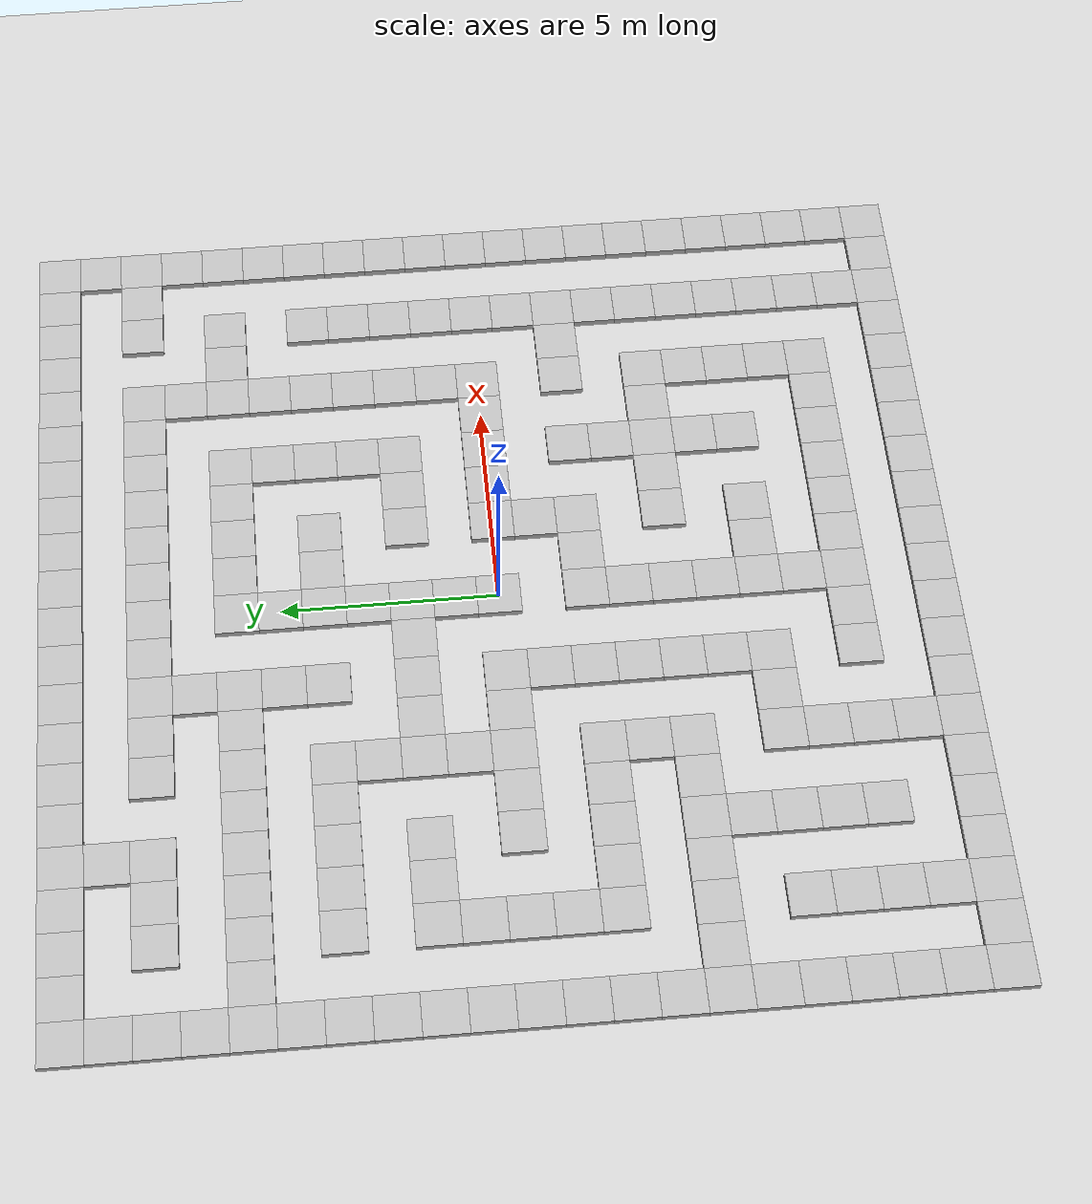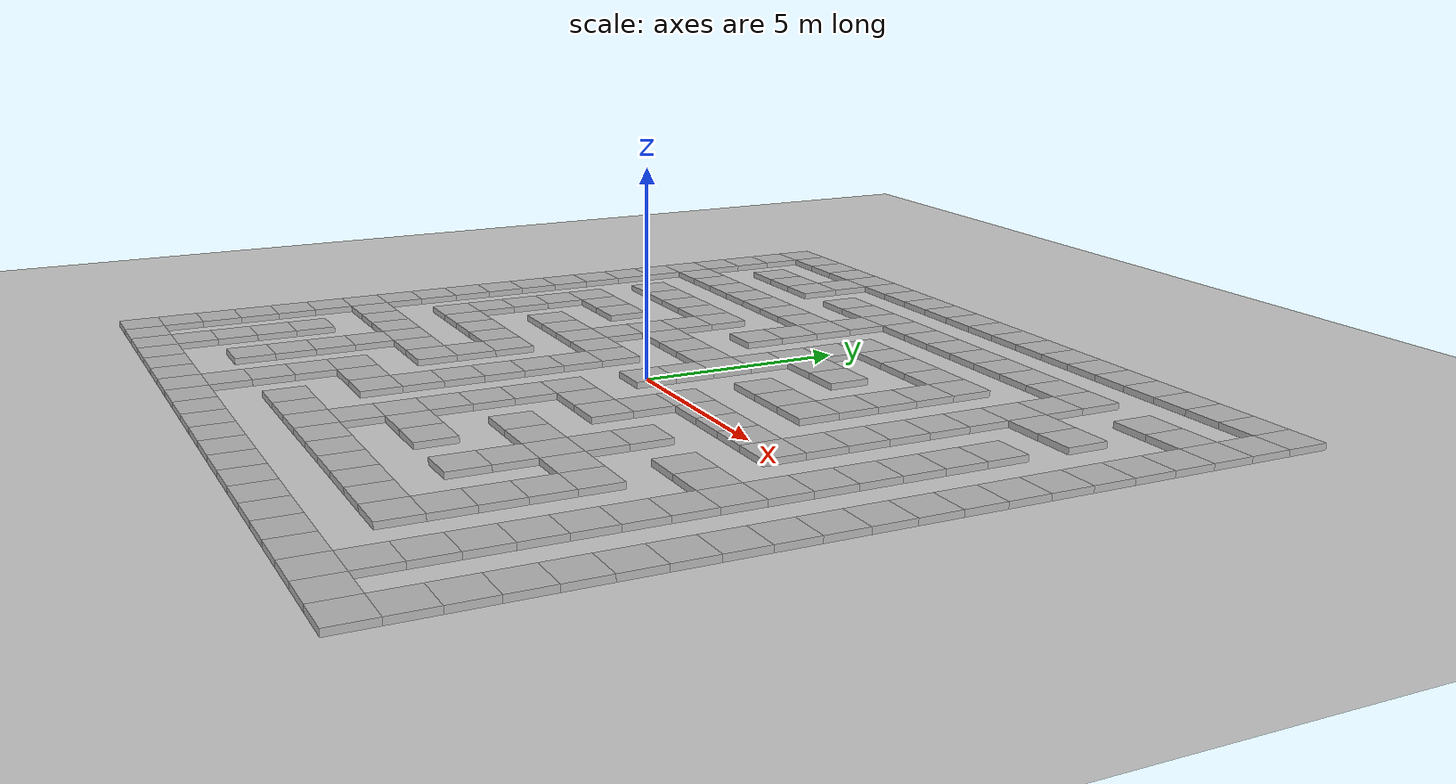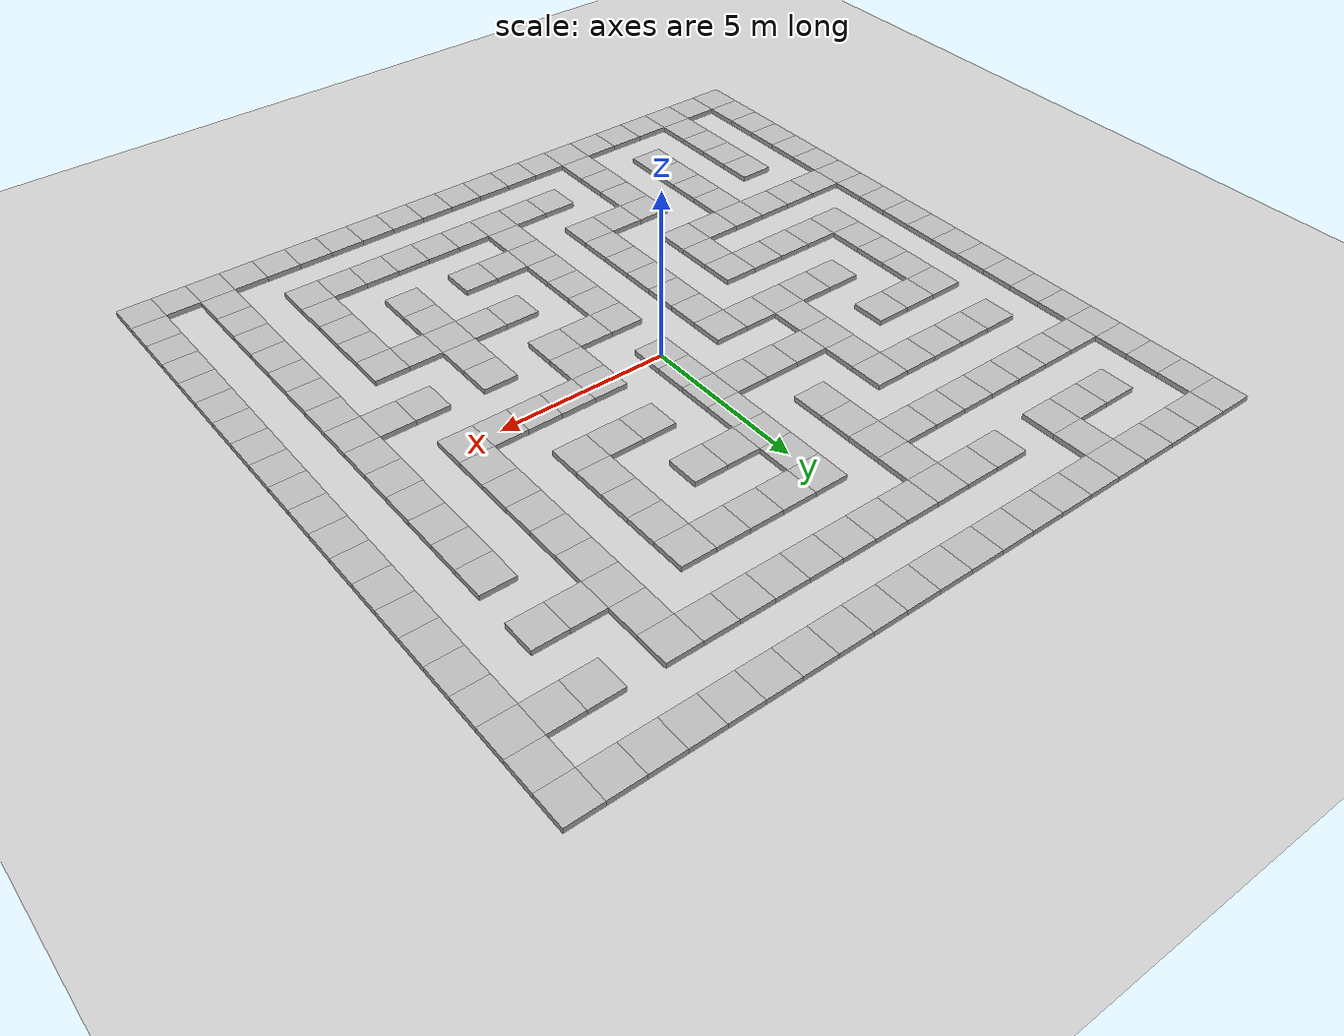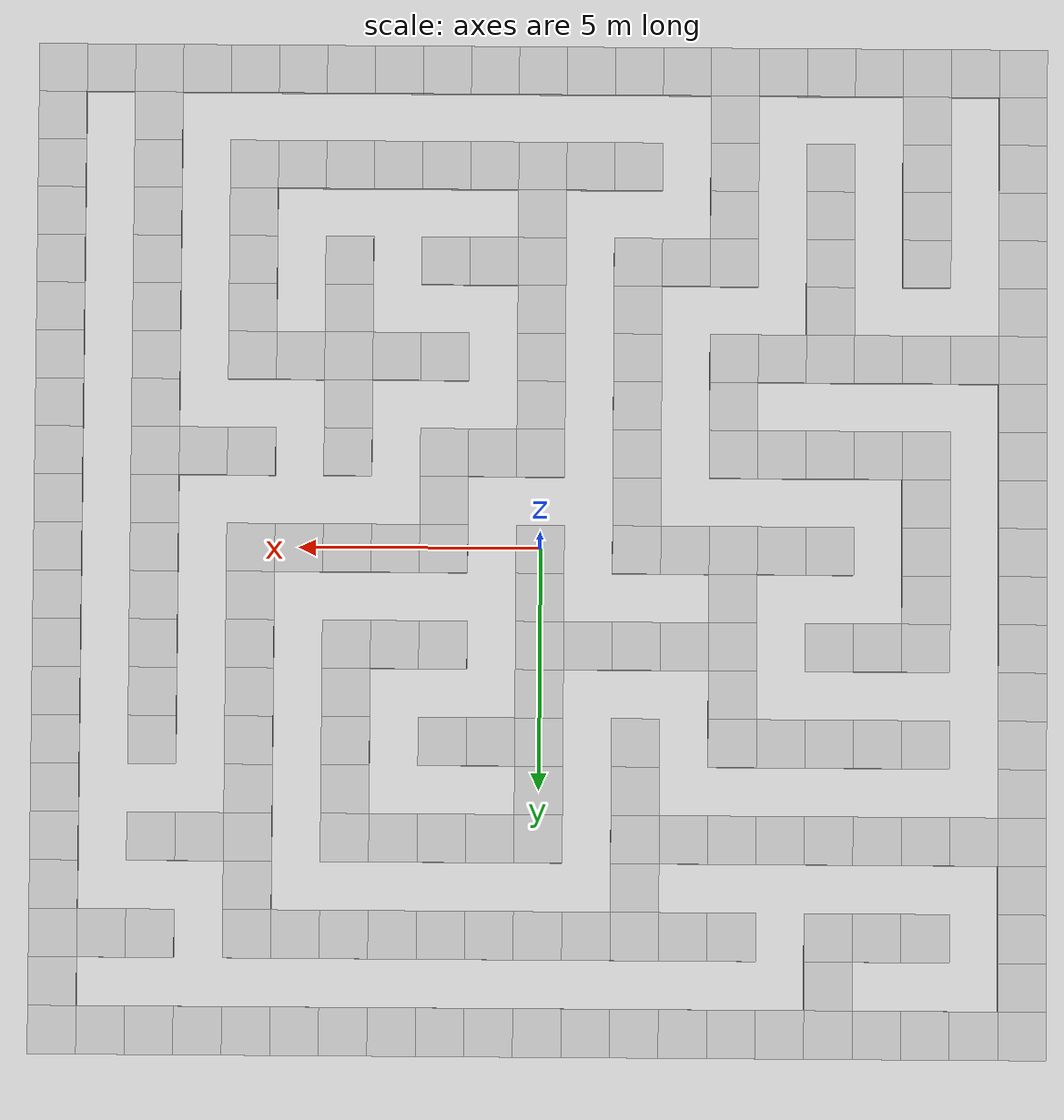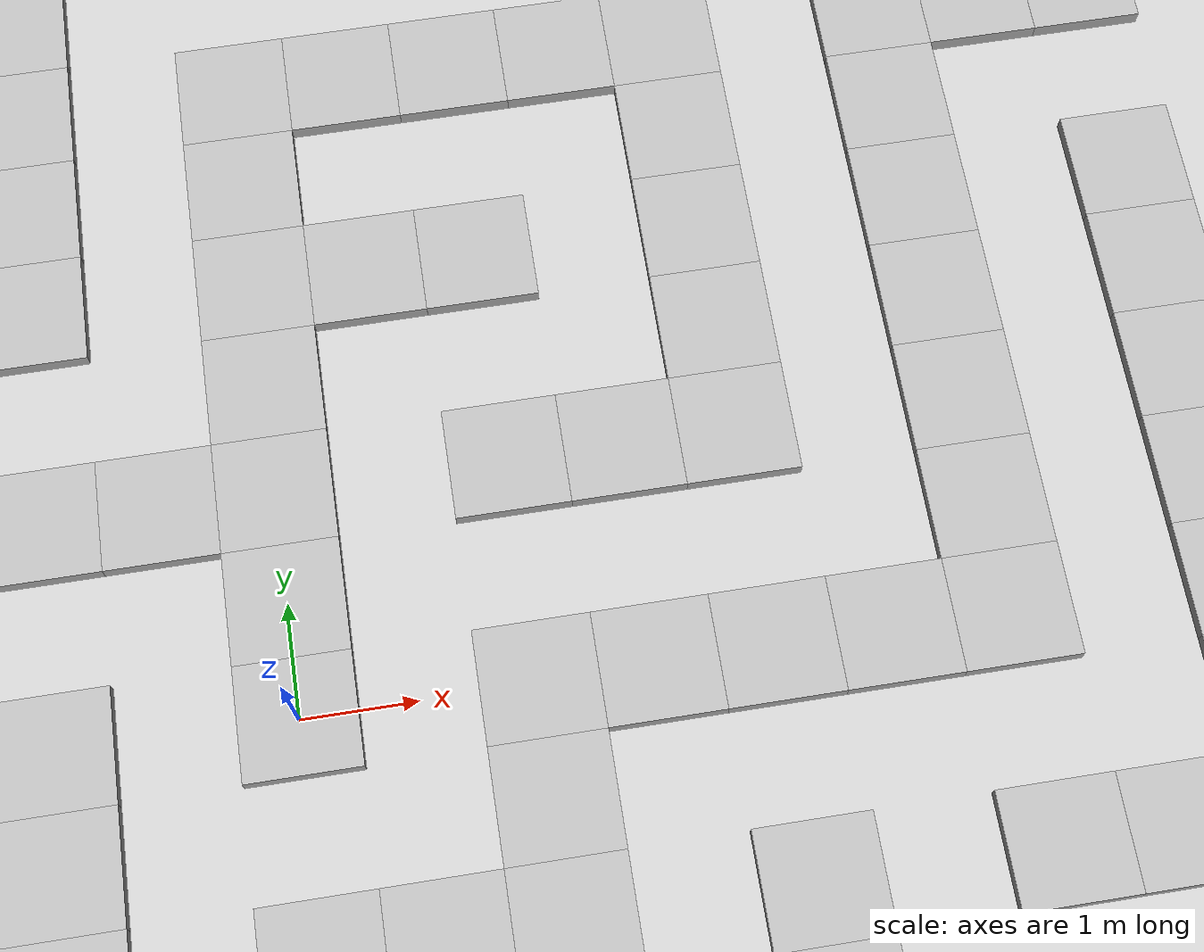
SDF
<sdf version="1.8">
    <world name="custom">
        <physics name="1ms" type="ignored">
            <max_step_size>0.001</max_step_size>
            <real_time_factor>1</real_time_factor>
            <real_time_update_rate>1000</real_time_update_rate>
        </physics>
        <plugin name="gz::sim::systems::Physics" filename="gz-sim-physics-system"/>
        <plugin name="gz::sim::systems::UserCommands" filename="gz-sim-user-commands-system"/>
        <plugin name="gz::sim::systems::SceneBroadcaster" filename="gz-sim-scene-broadcaster-system"/>
        <plugin name="gz::sim::systems::Contact" filename="gz-sim-contact-system"/>
        <light name="sun" type="directional">
            <cast_shadows>1</cast_shadows>
            <pose>0 0 10 0 -0 0</pose>
            <diffuse>0.8 0.8 0.8 1</diffuse>
            <specular>0.2 0.2 0.2 1</specular>
            <attenuation>
                <range>1000</range>
                <constant>0.90000000000000002</constant>
                <linear>0.01</linear>
                <quadratic>0.001</quadratic>
            </attenuation>
            <direction>-0.5 0.1 -0.9</direction>
            <spot>
                <inner_angle>0</inner_angle>
                <outer_angle>0</outer_angle>
                <falloff>0</falloff>
            </spot>
        </light>
        <gravity>0 0 -9.8</gravity>
        <magnetic_field>6e-06 2.3e-05 -4.2e-05</magnetic_field>
        <atmosphere type="adiabatic"/>
        <scene>
            <ambient>0.4 0.4 0.4 1</ambient>
            <background>0.7 0.7 0.7 1</background>
            <shadows>1</shadows>
        </scene>
        <model name="ground_plane">
            <static>1</static>
            <link name="link">
                <collision name="collision">
                    <geometry>
                        <plane>
                            <normal>0 0 1</normal>
                            <size>100 100</size>
                        </plane>
                    </geometry>
                    <surface>
                        <friction>
                            <ode/>
                        </friction>
                        <bounce/>
                        <contact/>
                    </surface>
                </collision>
                <visual name="visual">
                    <geometry>
                        <plane>
                            <normal>0 0 1</normal>
                            <size>100 100</size>
                        </plane>
                    </geometry>
                    <material>
                        <ambient>0.8 0.8 0.8 1</ambient>
                        <diffuse>0.8 0.8 0.8 1</diffuse>
                        <specular>0.8 0.8 0.8 1</specular>
                    </material>
                    <plugin name="__default__" filename="__default__"/>
                </visual>
            </link>
            <plugin name="__default__" filename="__default__"/>
            <pose>0 0 0 0 -0 0</pose>
        </model>
        <model name="border">
            <pose>0 0 1 0 0 0</pose>
            <static>true</static>
        </model>
        <model name="obstacles">
            <pose>0 0 0.5 0 0 0</pose>
            <static>true</static>
            <link name="wall1">
                <pose>-2 -10 -0.5 0 0 0</pose>
                <collision name="wall1_collision">
                    <geometry>
                        <box>
                            <size>1 1 0.25</size>
                        </box>
                    </geometry>
                </collision>
                <visual name="wall1_visual">
                    <geometry>
                        <box>
                            <size>1 1 0.25</size>
                        </box>
                    </geometry>
                </visual>
            </link>
            <link name="wall2">
                <pose>9 -10 -0.5 0 0 0</pose>
                <collision name="wall2_collision">
                    <geometry>
                        <box>
                            <size>1 1 0.25</size>
                        </box>
                    </geometry>
                </collision>
                <visual name="wall2_visual">
                    <geometry>
                        <box>
                            <size>1 1 0.25</size>
                        </box>
                    </geometry>
                </visual>
            </link>
            <link name="wall3">
                <pose>-2 -1 -0.5 0 0 0</pose>
                <collision name="wall3_collision">
                    <geometry>
                        <box>
                            <size>1 1 0.25</size>
                        </box>
                    </geometry>
                </collision>
                <visual name="wall3_visual">
                    <geometry>
                        <box>
                            <size>1 1 0.25</size>
                        </box>
                    </geometry>
                </visual>
            </link>
            <link name="wall4">
                <pose>-10 -5 -0.5 0 0 0</pose>
                <collision name="wall4_collision">
                    <geometry>
                        <box>
                            <size>1 1 0.25</size>
                        </box>
                    </geometry>
                </collision>
                <visual name="wall4_visual">
                    <geometry>
                        <box>
                            <size>1 1 0.25</size>
                        </box>
                    </geometry>
                </visual>
            </link>
            <link name="wall5">
                <pose>-2 8 -0.5 0 0 0</pose>
                <collision name="wall5_collision">
                    <geometry>
                        <box>
                            <size>1 1 0.25</size>
                        </box>
                    </geometry>
                </collision>
                <visual name="wall5_visual">
                    <geometry>
                        <box>
                            <size>1 1 0.25</size>
                        </box>
                    </geometry>
                </visual>
            </link>
            <link name="wall6">
                <pose>9 8 -0.5 0 0 0</pose>
                <collision name="wall6_collision">
                    <geometry>
                        <box>
                            <size>1 1 0.25</size>
                        </box>
                    </geometry>
                </collision>
                <visual name="wall6_visual">
                    <geometry>
                        <box>
                            <size>1 1 0.25</size>
                        </box>
                    </geometry>
                </visual>
            </link>
            <link name="wall7">
                <pose>-10 4 -0.5 0 0 0</pose>
                <collision name="wall7_collision">
                    <geometry>
                        <box>
                            <size>1 1 0.25</size>
                        </box>
                    </geometry>
                </collision>
                <visual name="wall7_visual">
                    <geometry>
                        <box>
                            <size>1 1 0.25</size>
                        </box>
                    </geometry>
                </visual>
            </link>
            <link name="wall8">
                <pose>1 4 -0.5 0 0 0</pose>
                <collision name="wall8_collision">
                    <geometry>
                        <box>
                            <size>1 1 0.25</size>
                        </box>
                    </geometry>
                </collision>
                <visual name="wall8_visual">
                    <geometry>
                        <box>
                            <size>1 1 0.25</size>
                        </box>
                    </geometry>
                </visual>
            </link>
            <link name="wall9">
                <pose>-6 -8 -0.5 0 0 0</pose>
                <collision name="wall9_collision">
                    <geometry>
                        <box>
                            <size>1 1 0.25</size>
                        </box>
                    </geometry>
                </collision>
                <visual name="wall9_visual">
                    <geometry>
                        <box>
                            <size>1 1 0.25</size>
                        </box>
                    </geometry>
                </visual>
            </link>
            <link name="wall10">
                <pose>-7 -4 -0.5 0 0 0</pose>
                <collision name="wall10_collision">
                    <geometry>
                        <box>
                            <size>1 1 0.25</size>
                        </box>
                    </geometry>
                </collision>
                <visual name="wall10_visual">
                    <geometry>
                        <box>
                            <size>1 1 0.25</size>
                        </box>
                    </geometry>
                </visual>
            </link>
            <link name="wall11">
                <pose>4 5 -0.5 0 0 0</pose>
                <collision name="wall11_collision">
                    <geometry>
                        <box>
                            <size>1 1 0.25</size>
                        </box>
                    </geometry>
                </collision>
                <visual name="wall11_visual">
                    <geometry>
                        <box>
                            <size>1 1 0.25</size>
                        </box>
                    </geometry>
                </visual>
            </link>
            <link name="wall12">
                <pose>8 -7 -0.5 0 0 0</pose>
                <collision name="wall12_collision">
                    <geometry>
                        <box>
                            <size>1 1 0.25</size>
                        </box>
                    </geometry>
                </collision>
                <visual name="wall12_visual">
                    <geometry>
                        <box>
                            <size>1 1 0.25</size>
                        </box>
                    </geometry>
                </visual>
            </link>
            <link name="wall13">
                <pose>-3 2 -0.5 0 0 0</pose>
                <collision name="wall13_collision">
                    <geometry>
                        <box>
                            <size>1 1 0.25</size>
                        </box>
                    </geometry>
                </collision>
                <visual name="wall13_visual">
                    <geometry>
                        <box>
                            <size>1 1 0.25</size>
                        </box>
                    </geometry>
                </visual>
            </link>
            <link name="wall14">
                <pose>8 2 -0.5 0 0 0</pose>
                <collision name="wall14_collision">
                    <geometry>
                        <box>
                            <size>1 1 0.25</size>
                        </box>
                    </geometry>
                </collision>
                <visual name="wall14_visual">
                    <geometry>
                        <box>
                            <size>1 1 0.25</size>
                        </box>
                    </geometry>
                </visual>
            </link>
            <link name="wall15">
                <pose>-2 -6 -0.5 0 0 0</pose>
                <collision name="wall15_collision">
                    <geometry>
                        <box>
                            <size>1 1 0.25</size>
                        </box>
                    </geometry>
                </collision>
                <visual name="wall15_visual">
                    <geometry>
                        <box>
                            <size>1 1 0.25</size>
                        </box>
                    </geometry>
                </visual>
            </link>
            <link name="wall16">
                <pose>-10 -10 -0.5 0 0 0</pose>
                <collision name="wall16_collision">
                    <geometry>
                        <box>
                            <size>1 1 0.25</size>
                        </box>
                    </geometry>
                </collision>
                <visual name="wall16_visual">
                    <geometry>
                        <box>
                            <size>1 1 0.25</size>
                        </box>
                    </geometry>
                </visual>
            </link>
            <link name="wall17">
                <pose>1 -10 -0.5 0 0 0</pose>
                <collision name="wall17_collision">
                    <geometry>
                        <box>
                            <size>1 1 0.25</size>
                        </box>
                    </geometry>
                </collision>
                <visual name="wall17_visual">
                    <geometry>
                        <box>
                            <size>1 1 0.25</size>
                        </box>
                    </geometry>
                </visual>
            </link>
            <link name="wall18">
                <pose>-10 -1 -0.5 0 0 0</pose>
                <collision name="wall18_collision">
                    <geometry>
                        <box>
                            <size>1 1 0.25</size>
                        </box>
                    </geometry>
                </collision>
                <visual name="wall18_visual">
                    <geometry>
                        <box>
                            <size>1 1 0.25</size>
                        </box>
                    </geometry>
                </visual>
            </link>
            <link name="wall19">
                <pose>4 0 -0.5 0 0 0</pose>
                <collision name="wall19_collision">
                    <geometry>
                        <box>
                            <size>1 1 0.25</size>
                        </box>
                    </geometry>
                </collision>
                <visual name="wall19_visual">
                    <geometry>
                        <box>
                            <size>1 1 0.25</size>
                        </box>
                    </geometry>
                </visual>
            </link>
            <link name="wall20">
                <pose>5 -8 -0.5 0 0 0</pose>
                <collision name="wall20_collision">
                    <geometry>
                        <box>
                            <size>1 1 0.25</size>
                        </box>
                    </geometry>
                </collision>
                <visual name="wall20_visual">
                    <geometry>
                        <box>
                            <size>1 1 0.25</size>
                        </box>
                    </geometry>
                </visual>
            </link>
            <link name="wall21">
                <pose>8 -3 -0.5 0 0 0</pose>
                <collision name="wall21_collision">
                    <geometry>
                        <box>
                            <size>1 1 0.25</size>
                        </box>
                    </geometry>
                </collision>
                <visual name="wall21_visual">
                    <geometry>
                        <box>
                            <size>1 1 0.25</size>
                        </box>
                    </geometry>
                </visual>
            </link>
            <link name="wall22">
                <pose>-3 6 -0.5 0 0 0</pose>
                <collision name="wall22_collision">
                    <geometry>
                        <box>
                            <size>1 1 0.25</size>
                        </box>
                    </geometry>
                </collision>
                <visual name="wall22_visual">
                    <geometry>
                        <box>
                            <size>1 1 0.25</size>
                        </box>
                    </geometry>
                </visual>
            </link>
            <link name="wall23">
                <pose>8 6 -0.5 0 0 0</pose>
                <collision name="wall23_collision">
                    <geometry>
                        <box>
                            <size>1 1 0.25</size>
                        </box>
                    </geometry>
                </collision>
                <visual name="wall23_visual">
                    <geometry>
                        <box>
                            <size>1 1 0.25</size>
                        </box>
                    </geometry>
                </visual>
            </link>
            <link name="wall24">
                <pose>1 -6 -0.5 0 0 0</pose>
                <collision name="wall24_collision">
                    <geometry>
                        <box>
                            <size>1 1 0.25</size>
                        </box>
                    </geometry>
                </collision>
                <visual name="wall24_visual">
                    <geometry>
                        <box>
                            <size>1 1 0.25</size>
                        </box>
                    </geometry>
                </visual>
            </link>
            <link name="wall25">
                <pose>0 -2 -0.5 0 0 0</pose>
                <collision name="wall25_collision">
                    <geometry>
                        <box>
                            <size>1 1 0.25</size>
                        </box>
                    </geometry>
                </collision>
                <visual name="wall25_visual">
                    <geometry>
                        <box>
                            <size>1 1 0.25</size>
                        </box>
                    </geometry>
                </visual>
            </link>
            <link name="wall26">
                <pose>4 -5 -0.5 0 0 0</pose>
                <collision name="wall26_collision">
                    <geometry>
                        <box>
                            <size>1 1 0.25</size>
                        </box>
                    </geometry>
                </collision>
                <visual name="wall26_visual">
                    <geometry>
                        <box>
                            <size>1 1 0.25</size>
                        </box>
                    </geometry>
                </visual>
            </link>
            <link name="wall27">
                <pose>-7 4 -0.5 0 0 0</pose>
                <collision name="wall27_collision">
                    <geometry>
                        <box>
                            <size>1 1 0.25</size>
                        </box>
                    </geometry>
                </collision>
                <visual name="wall27_visual">
                    <geometry>
                        <box>
                            <size>1 1 0.25</size>
                        </box>
                    </geometry>
                </visual>
            </link>
            <link name="wall28">
                <pose>4 4 -0.5 0 0 0</pose>
                <collision name="wall28_collision">
                    <geometry>
                        <box>
                            <size>1 1 0.25</size>
                        </box>
                    </geometry>
                </collision>
                <visual name="wall28_visual">
                    <geometry>
                        <box>
                            <size>1 1 0.25</size>
                        </box>
                    </geometry>
                </visual>
            </link>
            <link name="wall29">
                <pose>5 -4 -0.5 0 0 0</pose>
                <collision name="wall29_collision">
                    <geometry>
                        <box>
                            <size>1 1 0.25</size>
                        </box>
                    </geometry>
                </collision>
                <visual name="wall29_visual">
                    <geometry>
                        <box>
                            <size>1 1 0.25</size>
                        </box>
                    </geometry>
                </visual>
            </link>
            <link name="wall30">
                <pose>8 -8 -0.5 0 0 0</pose>
                <collision name="wall30_collision">
                    <geometry>
                        <box>
                            <size>1 1 0.25</size>
                        </box>
                    </geometry>
                </collision>
                <visual name="wall30_visual">
                    <geometry>
                        <box>
                            <size>1 1 0.25</size>
                        </box>
                    </geometry>
                </visual>
            </link>
            <link name="wall31">
                <pose>8 1 -0.5 0 0 0</pose>
                <collision name="wall31_collision">
                    <geometry>
                        <box>
                            <size>1 1 0.25</size>
                        </box>
                    </geometry>
                </collision>
                <visual name="wall31_visual">
                    <geometry>
                        <box>
                            <size>1 1 0.25</size>
                        </box>
                    </geometry>
                </visual>
            </link>
            <link name="wall32">
                <pose>0 -7 -0.5 0 0 0</pose>
                <collision name="wall32_collision">
                    <geometry>
                        <box>
                            <size>1 1 0.25</size>
                        </box>
                    </geometry>
                </collision>
                <visual name="wall32_visual">
                    <geometry>
                        <box>
                            <size>1 1 0.25</size>
                        </box>
                    </geometry>
                </visual>
            </link>
            <link name="wall33">
                <pose>0 2 -0.5 0 0 0</pose>
                <collision name="wall33_collision">
                    <geometry>
                        <box>
                            <size>1 1 0.25</size>
                        </box>
                    </geometry>
                </collision>
                <visual name="wall33_visual">
                    <geometry>
                        <box>
                            <size>1 1 0.25</size>
                        </box>
                    </geometry>
                </visual>
            </link>
            <link name="wall34">
                <pose>-8 -2 -0.5 0 0 0</pose>
                <collision name="wall34_collision">
                    <geometry>
                        <box>
                            <size>1 1 0.25</size>
                        </box>
                    </geometry>
                </collision>
                <visual name="wall34_visual">
                    <geometry>
                        <box>
                            <size>1 1 0.25</size>
                        </box>
                    </geometry>
                </visual>
            </link>
            <link name="wall35">
                <pose>-7 -10 -0.5 0 0 0</pose>
                <collision name="wall35_collision">
                    <geometry>
                        <box>
                            <size>1 1 0.25</size>
                        </box>
                    </geometry>
                </collision>
                <visual name="wall35_visual">
                    <geometry>
                        <box>
                            <size>1 1 0.25</size>
                        </box>
                    </geometry>
                </visual>
            </link>
            <link name="wall36">
                <pose>4 -10 -0.5 0 0 0</pose>
                <collision name="wall36_collision">
                    <geometry>
                        <box>
                            <size>1 1 0.25</size>
                        </box>
                    </geometry>
                </collision>
                <visual name="wall36_visual">
                    <geometry>
                        <box>
                            <size>1 1 0.25</size>
                        </box>
                    </geometry>
                </visual>
            </link>
            <link name="wall37">
                <pose>-7 8 -0.5 0 0 0</pose>
                <collision name="wall37_collision">
                    <geometry>
                        <box>
                            <size>1 1 0.25</size>
                        </box>
                    </geometry>
                </collision>
                <visual name="wall37_visual">
                    <geometry>
                        <box>
                            <size>1 1 0.25</size>
                        </box>
                    </geometry>
                </visual>
            </link>
            <link name="wall38">
                <pose>4 8 -0.5 0 0 0</pose>
                <collision name="wall38_collision">
                    <geometry>
                        <box>
                            <size>1 1 0.25</size>
                        </box>
                    </geometry>
                </collision>
                <visual name="wall38_visual">
                    <geometry>
                        <box>
                            <size>1 1 0.25</size>
                        </box>
                    </geometry>
                </visual>
            </link>
            <link name="wall39">
                <pose>7 10 -0.5 0 0 0</pose>
                <collision name="wall39_collision">
                    <geometry>
                        <box>
                            <size>1 1 0.25</size>
                        </box>
                    </geometry>
                </collision>
                <visual name="wall39_visual">
                    <geometry>
                        <box>
                            <size>1 1 0.25</size>
                        </box>
                    </geometry>
                </visual>
            </link>
            <link name="wall40">
                <pose>-4 0 -0.5 0 0 0</pose>
                <collision name="wall40_collision">
                    <geometry>
                        <box>
                            <size>1 1 0.25</size>
                        </box>
                    </geometry>
                </collision>
                <visual name="wall40_visual">
                    <geometry>
                        <box>
                            <size>1 1 0.25</size>
                        </box>
                    </geometry>
                </visual>
            </link>
            <link name="wall41">
                <pose>0 -3 -0.5 0 0 0</pose>
                <collision name="wall41_collision">
                    <geometry>
                        <box>
                            <size>1 1 0.25</size>
                        </box>
                    </geometry>
                </collision>
                <visual name="wall41_visual">
                    <geometry>
                        <box>
                            <size>1 1 0.25</size>
                        </box>
                    </geometry>
                </visual>
            </link>
            <link name="wall42">
                <pose>-8 -7 -0.5 0 0 0</pose>
                <collision name="wall42_collision">
                    <geometry>
                        <box>
                            <size>1 1 0.25</size>
                        </box>
                    </geometry>
                </collision>
                <visual name="wall42_visual">
                    <geometry>
                        <box>
                            <size>1 1 0.25</size>
                        </box>
                    </geometry>
                </visual>
            </link>
            <link name="wall43">
                <pose>0 6 -0.5 0 0 0</pose>
                <collision name="wall43_collision">
                    <geometry>
                        <box>
                            <size>1 1 0.25</size>
                        </box>
                    </geometry>
                </collision>
                <visual name="wall43_visual">
                    <geometry>
                        <box>
                            <size>1 1 0.25</size>
                        </box>
                    </geometry>
                </visual>
            </link>
            <link name="wall44">
                <pose>-8 2 -0.5 0 0 0</pose>
                <collision name="wall44_collision">
                    <geometry>
                        <box>
                            <size>1 1 0.25</size>
                        </box>
                    </geometry>
                </collision>
                <visual name="wall44_visual">
                    <geometry>
                        <box>
                            <size>1 1 0.25</size>
                        </box>
                    </geometry>
                </visual>
            </link>
            <link name="wall45">
                <pose>4 -6 -0.5 0 0 0</pose>
                <collision name="wall45_collision">
                    <geometry>
                        <box>
                            <size>1 1 0.25</size>
                        </box>
                    </geometry>
                </collision>
                <visual name="wall45_visual">
                    <geometry>
                        <box>
                            <size>1 1 0.25</size>
                        </box>
                    </geometry>
                </visual>
            </link>
            <link name="wall46">
                <pose>-1 10 -0.5 0 0 0</pose>
                <collision name="wall46_collision">
                    <geometry>
                        <box>
                            <size>1 1 0.25</size>
                        </box>
                    </geometry>
                </collision>
                <visual name="wall46_visual">
                    <geometry>
                        <box>
                            <size>1 1 0.25</size>
                        </box>
                    </geometry>
                </visual>
            </link>
            <link name="wall47">
                <pose>-4 4 -0.5 0 0 0</pose>
                <collision name="wall47_collision">
                    <geometry>
                        <box>
                            <size>1 1 0.25</size>
                        </box>
                    </geometry>
                </collision>
                <visual name="wall47_visual">
                    <geometry>
                        <box>
                            <size>1 1 0.25</size>
                        </box>
                    </geometry>
                </visual>
            </link>
            <link name="wall48">
                <pose>0 -8 -0.5 0 0 0</pose>
                <collision name="wall48_collision">
                    <geometry>
                        <box>
                            <size>1 1 0.25</size>
                        </box>
                    </geometry>
                </collision>
                <visual name="wall48_visual">
                    <geometry>
                        <box>
                            <size>1 1 0.25</size>
                        </box>
                    </geometry>
                </visual>
            </link>
            <link name="wall49">
                <pose>0 1 -0.5 0 0 0</pose>
                <collision name="wall49_collision">
                    <geometry>
                        <box>
                            <size>1 1 0.25</size>
                        </box>
                    </geometry>
                </collision>
                <visual name="wall49_visual">
                    <geometry>
                        <box>
                            <size>1 1 0.25</size>
                        </box>
                    </geometry>
                </visual>
            </link>
            <link name="wall50">
                <pose>-8 6 -0.5 0 0 0</pose>
                <collision name="wall50_collision">
                    <geometry>
                        <box>
                            <size>1 1 0.25</size>
                        </box>
                    </geometry>
                </collision>
                <visual name="wall50_visual">
                    <geometry>
                        <box>
                            <size>1 1 0.25</size>
                        </box>
                    </geometry>
                </visual>
            </link>
            <link name="wall51">
                <pose>6 8 -0.5 0 0 0</pose>
                <collision name="wall51_collision">
                    <geometry>
                        <box>
                            <size>1 1 0.25</size>
                        </box>
                    </geometry>
                </collision>
                <visual name="wall51_visual">
                    <geometry>
                        <box>
                            <size>1 1 0.25</size>
                        </box>
                    </geometry>
                </visual>
            </link>
            <link name="wall52">
                <pose>-5 -2 -0.5 0 0 0</pose>
                <collision name="wall52_collision">
                    <geometry>
                        <box>
                            <size>1 1 0.25</size>
                        </box>
                    </geometry>
                </collision>
                <visual name="wall52_visual">
                    <geometry>
                        <box>
                            <size>1 1 0.25</size>
                        </box>
                    </geometry>
                </visual>
            </link>
            <link name="wall53">
                <pose>-4 -10 -0.5 0 0 0</pose>
                <collision name="wall53_collision">
                    <geometry>
                        <box>
                            <size>1 1 0.25</size>
                        </box>
                    </geometry>
                </collision>
                <visual name="wall53_visual">
                    <geometry>
                        <box>
                            <size>1 1 0.25</size>
                        </box>
                    </geometry>
                </visual>
            </link>
            <link name="wall54">
                <pose>-4 8 -0.5 0 0 0</pose>
                <collision name="wall54_collision">
                    <geometry>
                        <box>
                            <size>1 1 0.25</size>
                        </box>
                    </geometry>
                </collision>
                <visual name="wall54_visual">
                    <geometry>
                        <box>
                            <size>1 1 0.25</size>
                        </box>
                    </geometry>
                </visual>
            </link>
            <link name="wall55">
                <pose>10 10 -0.5 0 0 0</pose>
                <collision name="wall55_collision">
                    <geometry>
                        <box>
                            <size>1 1 0.25</size>
                        </box>
                    </geometry>
                </collision>
                <visual name="wall55_visual">
                    <geometry>
                        <box>
                            <size>1 1 0.25</size>
                        </box>
                    </geometry>
                </visual>
            </link>
            <link name="wall56">
                <pose>0 -4 -0.5 0 0 0</pose>
                <collision name="wall56_collision">
                    <geometry>
                        <box>
                            <size>1 1 0.25</size>
                        </box>
                    </geometry>
                </collision>
                <visual name="wall56_visual">
                    <geometry>
                        <box>
                            <size>1 1 0.25</size>
                        </box>
                    </geometry>
                </visual>
            </link>
            <link name="wall57">
                <pose>-8 -8 -0.5 0 0 0</pose>
                <collision name="wall57_collision">
                    <geometry>
                        <box>
                            <size>1 1 0.25</size>
                        </box>
                    </geometry>
                </collision>
                <visual name="wall57_visual">
                    <geometry>
                        <box>
                            <size>1 1 0.25</size>
                        </box>
                    </geometry>
                </visual>
            </link>
            <link name="wall58">
                <pose>-8 1 -0.5 0 0 0</pose>
                <collision name="wall58_collision">
                    <geometry>
                        <box>
                            <size>1 1 0.25</size>
                        </box>
                    </geometry>
                </collision>
                <visual name="wall58_visual">
                    <geometry>
                        <box>
                            <size>1 1 0.25</size>
                        </box>
                    </geometry>
                </visual>
            </link>
            <link name="wall59">
                <pose>6 3 -0.5 0 0 0</pose>
                <collision name="wall59_collision">
                    <geometry>
                        <box>
                            <size>1 1 0.25</size>
                        </box>
                    </geometry>
                </collision>
                <visual name="wall59_visual">
                    <geometry>
                        <box>
                            <size>1 1 0.25</size>
                        </box>
                    </geometry>
                </visual>
            </link>
            <link name="wall60">
                <pose>-4 -6 -0.5 0 0 0</pose>
                <collision name="wall60_collision">
                    <geometry>
                        <box>
                            <size>1 1 0.25</size>
                        </box>
                    </geometry>
                </collision>
                <visual name="wall60_visual">
                    <geometry>
                        <box>
                            <size>1 1 0.25</size>
                        </box>
                    </geometry>
                </visual>
            </link>
            <link name="wall61">
                <pose>-4 3 -0.5 0 0 0</pose>
                <collision name="wall61_collision">
                    <geometry>
                        <box>
                            <size>1 1 0.25</size>
                        </box>
                    </geometry>
                </collision>
                <visual name="wall61_visual">
                    <geometry>
                        <box>
                            <size>1 1 0.25</size>
                        </box>
                    </geometry>
                </visual>
            </link>
            <link name="wall62">
                <pose>10 5 -0.5 0 0 0</pose>
                <collision name="wall62_collision">
                    <geometry>
                        <box>
                            <size>1 1 0.25</size>
                        </box>
                    </geometry>
                </collision>
                <visual name="wall62_visual">
                    <geometry>
                        <box>
                            <size>1 1 0.25</size>
                        </box>
                    </geometry>
                </visual>
            </link>
            <link name="wall63">
                <pose>2 10 -0.5 0 0 0</pose>
                <collision name="wall63_collision">
                    <geometry>
                        <box>
                            <size>1 1 0.25</size>
                        </box>
                    </geometry>
                </collision>
                <visual name="wall63_visual">
                    <geometry>
                        <box>
                            <size>1 1 0.25</size>
                        </box>
                    </geometry>
                </visual>
            </link>
            <link name="wall64">
                <pose>3 2 -0.5 0 0 0</pose>
                <collision name="wall64_collision">
                    <geometry>
                        <box>
                            <size>1 1 0.25</size>
                        </box>
                    </geometry>
                </collision>
                <visual name="wall64_visual">
                    <geometry>
                        <box>
                            <size>1 1 0.25</size>
                        </box>
                    </geometry>
                </visual>
            </link>
            <link name="wall65">
                <pose>6 -2 -0.5 0 0 0</pose>
                <collision name="wall65_collision">
                    <geometry>
                        <box>
                            <size>1 1 0.25</size>
                        </box>
                    </geometry>
                </collision>
                <visual name="wall65_visual">
                    <geometry>
                        <box>
                            <size>1 1 0.25</size>
                        </box>
                    </geometry>
                </visual>
            </link>
            <link name="wall66">
                <pose>6 7 -0.5 0 0 0</pose>
                <collision name="wall66_collision">
                    <geometry>
                        <box>
                            <size>1 1 0.25</size>
                        </box>
                    </geometry>
                </collision>
                <visual name="wall66_visual">
                    <geometry>
                        <box>
                            <size>1 1 0.25</size>
                        </box>
                    </geometry>
                </visual>
            </link>
            <link name="wall67">
                <pose>7 -10 -0.5 0 0 0</pose>
                <collision name="wall67_collision">
                    <geometry>
                        <box>
                            <size>1 1 0.25</size>
                        </box>
                    </geometry>
                </collision>
                <visual name="wall67_visual">
                    <geometry>
                        <box>
                            <size>1 1 0.25</size>
                        </box>
                    </geometry>
                </visual>
            </link>
            <link name="wall68">
                <pose>-5 6 -0.5 0 0 0</pose>
                <collision name="wall68_collision">
                    <geometry>
                        <box>
                            <size>1 1 0.25</size>
                        </box>
                    </geometry>
                </collision>
                <visual name="wall68_visual">
                    <geometry>
                        <box>
                            <size>1 1 0.25</size>
                        </box>
                    </geometry>
                </visual>
            </link>
            <link name="wall69">
                <pose>10 -9 -0.5 0 0 0</pose>
                <collision name="wall69_collision">
                    <geometry>
                        <box>
                            <size>1 1 0.25</size>
                        </box>
                    </geometry>
                </collision>
                <visual name="wall69_visual">
                    <geometry>
                        <box>
                            <size>1 1 0.25</size>
                        </box>
                    </geometry>
                </visual>
            </link>
            <link name="wall70">
                <pose>10 0 -0.5 0 0 0</pose>
                <collision name="wall70_collision">
                    <geometry>
                        <box>
                            <size>1 1 0.25</size>
                        </box>
                    </geometry>
                </collision>
                <visual name="wall70_visual">
                    <geometry>
                        <box>
                            <size>1 1 0.25</size>
                        </box>
                    </geometry>
                </visual>
            </link>
            <link name="wall71">
                <pose>2 -4 -0.5 0 0 0</pose>
                <collision name="wall71_collision">
                    <geometry>
                        <box>
                            <size>1 1 0.25</size>
                        </box>
                    </geometry>
                </collision>
                <visual name="wall71_visual">
                    <geometry>
                        <box>
                            <size>1 1 0.25</size>
                        </box>
                    </geometry>
                </visual>
            </link>
            <link name="wall72">
                <pose>10 9 -0.5 0 0 0</pose>
                <collision name="wall72_collision">
                    <geometry>
                        <box>
                            <size>1 1 0.25</size>
                        </box>
                    </geometry>
                </collision>
                <visual name="wall72_visual">
                    <geometry>
                        <box>
                            <size>1 1 0.25</size>
                        </box>
                    </geometry>
                </visual>
            </link>
            <link name="wall73">
                <pose>-6 10 -0.5 0 0 0</pose>
                <collision name="wall73_collision">
                    <geometry>
                        <box>
                            <size>1 1 0.25</size>
                        </box>
                    </geometry>
                </collision>
                <visual name="wall73_visual">
                    <geometry>
                        <box>
                            <size>1 1 0.25</size>
                        </box>
                    </geometry>
                </visual>
            </link>
            <link name="wall74">
                <pose>6 -7 -0.5 0 0 0</pose>
                <collision name="wall74_collision">
                    <geometry>
                        <box>
                            <size>1 1 0.25</size>
                        </box>
                    </geometry>
                </collision>
                <visual name="wall74_visual">
                    <geometry>
                        <box>
                            <size>1 1 0.25</size>
                        </box>
                    </geometry>
                </visual>
            </link>
            <link name="wall75">
                <pose>3 6 -0.5 0 0 0</pose>
                <collision name="wall75_collision">
                    <geometry>
                        <box>
                            <size>1 1 0.25</size>
                        </box>
                    </geometry>
                </collision>
                <visual name="wall75_visual">
                    <geometry>
                        <box>
                            <size>1 1 0.25</size>
                        </box>
                    </geometry>
                </visual>
            </link>
            <link name="wall76">
                <pose>6 2 -0.5 0 0 0</pose>
                <collision name="wall76_collision">
                    <geometry>
                        <box>
                            <size>1 1 0.25</size>
                        </box>
                    </geometry>
                </collision>
                <visual name="wall76_visual">
                    <geometry>
                        <box>
                            <size>1 1 0.25</size>
                        </box>
                    </geometry>
                </visual>
            </link>
            <link name="wall77">
                <pose>-1 -10 -0.5 0 0 0</pose>
                <collision name="wall77_collision">
                    <geometry>
                        <box>
                            <size>1 1 0.25</size>
                        </box>
                    </geometry>
                </collision>
                <visual name="wall77_visual">
                    <geometry>
                        <box>
                            <size>1 1 0.25</size>
                        </box>
                    </geometry>
                </visual>
            </link>
            <link name="wall78">
                <pose>-10 8 -0.5 0 0 0</pose>
                <collision name="wall78_collision">
                    <geometry>
                        <box>
                            <size>1 1 0.25</size>
                        </box>
                    </geometry>
                </collision>
                <visual name="wall78_visual">
                    <geometry>
                        <box>
                            <size>1 1 0.25</size>
                        </box>
                    </geometry>
                </visual>
            </link>
            <link name="wall79">
                <pose>1 8 -0.5 0 0 0</pose>
                <collision name="wall79_collision">
                    <geometry>
                        <box>
                            <size>1 1 0.25</size>
                        </box>
                    </geometry>
                </collision>
                <visual name="wall79_visual">
                    <geometry>
                        <box>
                            <size>1 1 0.25</size>
                        </box>
                    </geometry>
                </visual>
            </link>
            <link name="wall80">
                <pose>10 -5 -0.5 0 0 0</pose>
                <collision name="wall80_collision">
                    <geometry>
                        <box>
                            <size>1 1 0.25</size>
                        </box>
                    </geometry>
                </collision>
                <visual name="wall80_visual">
                    <geometry>
                        <box>
                            <size>1 1 0.25</size>
                        </box>
                    </geometry>
                </visual>
            </link>
            <link name="wall81">
                <pose>10 4 -0.5 0 0 0</pose>
                <collision name="wall81_collision">
                    <geometry>
                        <box>
                            <size>1 1 0.25</size>
                        </box>
                    </geometry>
                </collision>
                <visual name="wall81_visual">
                    <geometry>
                        <box>
                            <size>1 1 0.25</size>
                        </box>
                    </geometry>
                </visual>
            </link>
            <link name="wall82">
                <pose>2 0 -0.5 0 0 0</pose>
                <collision name="wall82_collision">
                    <geometry>
                        <box>
                            <size>1 1 0.25</size>
                        </box>
                    </geometry>
                </collision>
                <visual name="wall82_visual">
                    <geometry>
                        <box>
                            <size>1 1 0.25</size>
                        </box>
                    </geometry>
                </visual>
            </link>
            <link name="wall83">
                <pose>-6 -4 -0.5 0 0 0</pose>
                <collision name="wall83_collision">
                    <geometry>
                        <box>
                            <size>1 1 0.25</size>
                        </box>
                    </geometry>
                </collision>
                <visual name="wall83_visual">
                    <geometry>
                        <box>
                            <size>1 1 0.25</size>
                        </box>
                    </geometry>
                </visual>
            </link>
            <link name="wall84">
                <pose>-9 -10 -0.5 0 0 0</pose>
                <collision name="wall84_collision">
                    <geometry>
                        <box>
                            <size>1 1 0.25</size>
                        </box>
                    </geometry>
                </collision>
                <visual name="wall84_visual">
                    <geometry>
                        <box>
                            <size>1 1 0.25</size>
                        </box>
                    </geometry>
                </visual>
            </link>
            <link name="wall85">
                <pose>3 -8 -0.5 0 0 0</pose>
                <collision name="wall85_collision">
                    <geometry>
                        <box>
                            <size>1 1 0.25</size>
                        </box>
                    </geometry>
                </collision>
                <visual name="wall85_visual">
                    <geometry>
                        <box>
                            <size>1 1 0.25</size>
                        </box>
                    </geometry>
                </visual>
            </link>
            <link name="wall86">
                <pose>6 6 -0.5 0 0 0</pose>
                <collision name="wall86_collision">
                    <geometry>
                        <box>
                            <size>1 1 0.25</size>
                        </box>
                    </geometry>
                </collision>
                <visual name="wall86_visual">
                    <geometry>
                        <box>
                            <size>1 1 0.25</size>
                        </box>
                    </geometry>
                </visual>
            </link>
            <link name="wall87">
                <pose>5 10 -0.5 0 0 0</pose>
                <collision name="wall87_collision">
                    <geometry>
                        <box>
                            <size>1 1 0.25</size>
                        </box>
                    </geometry>
                </collision>
                <visual name="wall87_visual">
                    <geometry>
                        <box>
                            <size>1 1 0.25</size>
                        </box>
                    </geometry>
                </visual>
            </link>
            <link name="wall88">
                <pose>-5 -4 -0.5 0 0 0</pose>
                <collision name="wall88_collision">
                    <geometry>
                        <box>
                            <size>1 1 0.25</size>
                        </box>
                    </geometry>
                </collision>
                <visual name="wall88_visual">
                    <geometry>
                        <box>
                            <size>1 1 0.25</size>
                        </box>
                    </geometry>
                </visual>
            </link>
            <link name="wall89">
                <pose>8 -2 -0.5 0 0 0</pose>
                <collision name="wall89_collision">
                    <geometry>
                        <box>
                            <size>1 1 0.25</size>
                        </box>
                    </geometry>
                </collision>
                <visual name="wall89_visual">
                    <geometry>
                        <box>
                            <size>1 1 0.25</size>
                        </box>
                    </geometry>
                </visual>
            </link>
            <link name="wall90">
                <pose>-2 -2 -0.5 0 0 0</pose>
                <collision name="wall90_collision">
                    <geometry>
                        <box>
                            <size>1 1 0.25</size>
                        </box>
                    </geometry>
                </collision>
                <visual name="wall90_visual">
                    <geometry>
                        <box>
                            <size>1 1 0.25</size>
                        </box>
                    </geometry>
                </visual>
            </link>
            <link name="wall91">
                <pose>-10 -6 -0.5 0 0 0</pose>
                <collision name="wall91_collision">
                    <geometry>
                        <box>
                            <size>1 1 0.25</size>
                        </box>
                    </geometry>
                </collision>
                <visual name="wall91_visual">
                    <geometry>
                        <box>
                            <size>1 1 0.25</size>
                        </box>
                    </geometry>
                </visual>
            </link>
            <link name="wall92">
                <pose>-2 7 -0.5 0 0 0</pose>
                <collision name="wall92_collision">
                    <geometry>
                        <box>
                            <size>1 1 0.25</size>
                        </box>
                    </geometry>
                </collision>
                <visual name="wall92_visual">
                    <geometry>
                        <box>
                            <size>1 1 0.25</size>
                        </box>
                    </geometry>
                </visual>
            </link>
            <link name="wall93">
                <pose>-10 3 -0.5 0 0 0</pose>
                <collision name="wall93_collision">
                    <geometry>
                        <box>
                            <size>1 1 0.25</size>
                        </box>
                    </geometry>
                </collision>
                <visual name="wall93_visual">
                    <geometry>
                        <box>
                            <size>1 1 0.25</size>
                        </box>
                    </geometry>
                </visual>
            </link>
            <link name="wall94">
                <pose>10 -10 -0.5 0 0 0</pose>
                <collision name="wall94_collision">
                    <geometry>
                        <box>
                            <size>1 1 0.25</size>
                        </box>
                    </geometry>
                </collision>
                <visual name="wall94_visual">
                    <geometry>
                        <box>
                            <size>1 1 0.25</size>
                        </box>
                    </geometry>
                </visual>
            </link>
            <link name="wall95">
                <pose>10 -1 -0.5 0 0 0</pose>
                <collision name="wall95_collision">
                    <geometry>
                        <box>
                            <size>1 1 0.25</size>
                        </box>
                    </geometry>
                </collision>
                <visual name="wall95_visual">
                    <geometry>
                        <box>
                            <size>1 1 0.25</size>
                        </box>
                    </geometry>
                </visual>
            </link>
            <link name="wall96">
                <pose>10 8 -0.5 0 0 0</pose>
                <collision name="wall96_collision">
                    <geometry>
                        <box>
                            <size>1 1 0.25</size>
                        </box>
                    </geometry>
                </collision>
                <visual name="wall96_visual">
                    <geometry>
                        <box>
                            <size>1 1 0.25</size>
                        </box>
                    </geometry>
                </visual>
            </link>
            <link name="wall97">
                <pose>2 4 -0.5 0 0 0</pose>
                <collision name="wall97_collision">
                    <geometry>
                        <box>
                            <size>1 1 0.25</size>
                        </box>
                    </geometry>
                </collision>
                <visual name="wall97_visual">
                    <geometry>
                        <box>
                            <size>1 1 0.25</size>
                        </box>
                    </geometry>
                </visual>
            </link>
            <link name="wall98">
                <pose>-6 0 -0.5 0 0 0</pose>
                <collision name="wall98_collision">
                    <geometry>
                        <box>
                            <size>1 1 0.25</size>
                        </box>
                    </geometry>
                </collision>
                <visual name="wall98_visual">
                    <geometry>
                        <box>
                            <size>1 1 0.25</size>
                        </box>
                    </geometry>
                </visual>
            </link>
            <link name="wall99">
                <pose>-6 9 -0.5 0 0 0</pose>
                <collision name="wall99_collision">
                    <geometry>
                        <box>
                            <size>1 1 0.25</size>
                        </box>
                    </geometry>
                </collision>
                <visual name="wall99_visual">
                    <geometry>
                        <box>
                            <size>1 1 0.25</size>
                        </box>
                    </geometry>
                </visual>
            </link>
            <link name="wall100">
                <pose>6 -8 -0.5 0 0 0</pose>
                <collision name="wall100_collision">
                    <geometry>
                        <box>
                            <size>1 1 0.25</size>
                        </box>
                    </geometry>
                </collision>
                <visual name="wall100_visual">
                    <geometry>
                        <box>
                            <size>1 1 0.25</size>
                        </box>
                    </geometry>
                </visual>
            </link>
            <link name="wall101">
                <pose>-3 10 -0.5 0 0 0</pose>
                <collision name="wall101_collision">
                    <geometry>
                        <box>
                            <size>1 1 0.25</size>
                        </box>
                    </geometry>
                </collision>
                <visual name="wall101_visual">
                    <geometry>
                        <box>
                            <size>1 1 0.25</size>
                        </box>
                    </geometry>
                </visual>
            </link>
            <link name="wall102">
                <pose>8 10 -0.5 0 0 0</pose>
                <collision name="wall102_collision">
                    <geometry>
                        <box>
                            <size>1 1 0.25</size>
                        </box>
                    </geometry>
                </collision>
                <visual name="wall102_visual">
                    <geometry>
                        <box>
                            <size>1 1 0.25</size>
                        </box>
                    </geometry>
                </visual>
            </link>
            <link name="wall103">
                <pose>-2 2 -0.5 0 0 0</pose>
                <collision name="wall103_collision">
                    <geometry>
                        <box>
                            <size>1 1 0.25</size>
                        </box>
                    </geometry>
                </collision>
                <visual name="wall103_visual">
                    <geometry>
                        <box>
                            <size>1 1 0.25</size>
                        </box>
                    </geometry>
                </visual>
            </link>
            <link name="wall104">
                <pose>-10 -2 -0.5 0 0 0</pose>
                <collision name="wall104_collision">
                    <geometry>
                        <box>
                            <size>1 1 0.25</size>
                        </box>
                    </geometry>
                </collision>
                <visual name="wall104_visual">
                    <geometry>
                        <box>
                            <size>1 1 0.25</size>
                        </box>
                    </geometry>
                </visual>
            </link>
            <link name="wall105">
                <pose>1 -2 -0.5 0 0 0</pose>
                <collision name="wall105_collision">
                    <geometry>
                        <box>
                            <size>1 1 0.25</size>
                        </box>
                    </geometry>
                </collision>
                <visual name="wall105_visual">
                    <geometry>
                        <box>
                            <size>1 1 0.25</size>
                        </box>
                    </geometry>
                </visual>
            </link>
            <link name="wall106">
                <pose>-10 7 -0.5 0 0 0</pose>
                <collision name="wall106_collision">
                    <geometry>
                        <box>
                            <size>1 1 0.25</size>
                        </box>
                    </geometry>
                </collision>
                <visual name="wall106_visual">
                    <geometry>
                        <box>
                            <size>1 1 0.25</size>
                        </box>
                    </geometry>
                </visual>
            </link>
            <link name="wall107">
                <pose>10 -6 -0.5 0 0 0</pose>
                <collision name="wall107_collision">
                    <geometry>
                        <box>
                            <size>1 1 0.25</size>
                        </box>
                    </geometry>
                </collision>
                <visual name="wall107_visual">
                    <geometry>
                        <box>
                            <size>1 1 0.25</size>
                        </box>
                    </geometry>
                </visual>
            </link>
            <link name="wall108">
                <pose>2 -10 -0.5 0 0 0</pose>
                <collision name="wall108_collision">
                    <geometry>
                        <box>
                            <size>1 1 0.25</size>
                        </box>
                    </geometry>
                </collision>
                <visual name="wall108_visual">
                    <geometry>
                        <box>
                            <size>1 1 0.25</size>
                        </box>
                    </geometry>
                </visual>
            </link>
            <link name="wall109">
                <pose>10 3 -0.5 0 0 0</pose>
                <collision name="wall109_collision">
                    <geometry>
                        <box>
                            <size>1 1 0.25</size>
                        </box>
                    </geometry>
                </collision>
                <visual name="wall109_visual">
                    <geometry>
                        <box>
                            <size>1 1 0.25</size>
                        </box>
                    </geometry>
                </visual>
            </link>
            <link name="wall110">
                <pose>2 -1 -0.5 0 0 0</pose>
                <collision name="wall110_collision">
                    <geometry>
                        <box>
                            <size>1 1 0.25</size>
                        </box>
                    </geometry>
                </collision>
                <visual name="wall110_visual">
                    <geometry>
                        <box>
                            <size>1 1 0.25</size>
                        </box>
                    </geometry>
                </visual>
            </link>
            <link name="wall111">
                <pose>-6 -5 -0.5 0 0 0</pose>
                <collision name="wall111_collision">
                    <geometry>
                        <box>
                            <size>1 1 0.25</size>
                        </box>
                    </geometry>
                </collision>
                <visual name="wall111_visual">
                    <geometry>
                        <box>
                            <size>1 1 0.25</size>
                        </box>
                    </geometry>
                </visual>
            </link>
            <link name="wall112">
                <pose>-6 4 -0.5 0 0 0</pose>
                <collision name="wall112_collision">
                    <geometry>
                        <box>
                            <size>1 1 0.25</size>
                        </box>
                    </geometry>
                </collision>
                <visual name="wall112_visual">
                    <geometry>
                        <box>
                            <size>1 1 0.25</size>
                        </box>
                    </geometry>
                </visual>
            </link>
            <link name="wall113">
                <pose>5 0 -0.5 0 0 0</pose>
                <collision name="wall113_collision">
                    <geometry>
                        <box>
                            <size>1 1 0.25</size>
                        </box>
                    </geometry>
                </collision>
                <visual name="wall113_visual">
                    <geometry>
                        <box>
                            <size>1 1 0.25</size>
                        </box>
                    </geometry>
                </visual>
            </link>
            <link name="wall114">
                <pose>8 -4 -0.5 0 0 0</pose>
                <collision name="wall114_collision">
                    <geometry>
                        <box>
                            <size>1 1 0.25</size>
                        </box>
                    </geometry>
                </collision>
                <visual name="wall114_visual">
                    <geometry>
                        <box>
                            <size>1 1 0.25</size>
                        </box>
                    </geometry>
                </visual>
            </link>
            <link name="wall115">
                <pose>-2 -3 -0.5 0 0 0</pose>
                <collision name="wall115_collision">
                    <geometry>
                        <box>
                            <size>1 1 0.25</size>
                        </box>
                    </geometry>
                </collision>
                <visual name="wall115_visual">
                    <geometry>
                        <box>
                            <size>1 1 0.25</size>
                        </box>
                    </geometry>
                </visual>
            </link>
            <link name="wall116">
                <pose>-10 -7 -0.5 0 0 0</pose>
                <collision name="wall116_collision">
                    <geometry>
                        <box>
                            <size>1 1 0.25</size>
                        </box>
                    </geometry>
                </collision>
                <visual name="wall116_visual">
                    <geometry>
                        <box>
                            <size>1 1 0.25</size>
                        </box>
                    </geometry>
                </visual>
            </link>
            <link name="wall117">
                <pose>-2 6 -0.5 0 0 0</pose>
                <collision name="wall117_collision">
                    <geometry>
                        <box>
                            <size>1 1 0.25</size>
                        </box>
                    </geometry>
                </collision>
                <visual name="wall117_visual">
                    <geometry>
                        <box>
                            <size>1 1 0.25</size>
                        </box>
                    </geometry>
                </visual>
            </link>
            <link name="wall118">
                <pose>-10 2 -0.5 0 0 0</pose>
                <collision name="wall118_collision">
                    <geometry>
                        <box>
                            <size>1 1 0.25</size>
                        </box>
                    </geometry>
                </collision>
                <visual name="wall118_visual">
                    <geometry>
                        <box>
                            <size>1 1 0.25</size>
                        </box>
                    </geometry>
                </visual>
            </link>
            <link name="wall119">
                <pose>2 -6 -0.5 0 0 0</pose>
                <collision name="wall119_collision">
                    <geometry>
                        <box>
                            <size>1 1 0.25</size>
                        </box>
                    </geometry>
                </collision>
                <visual name="wall119_visual">
                    <geometry>
                        <box>
                            <size>1 1 0.25</size>
                        </box>
                    </geometry>
                </visual>
            </link>
            <link name="wall120">
                <pose>-6 -10 -0.5 0 0 0</pose>
                <collision name="wall120_collision">
                    <geometry>
                        <box>
                            <size>1 1 0.25</size>
                        </box>
                    </geometry>
                </collision>
                <visual name="wall120_visual">
                    <geometry>
                        <box>
                            <size>1 1 0.25</size>
                        </box>
                    </geometry>
                </visual>
            </link>
            <link name="wall121">
                <pose>4 3 -0.5 0 0 0</pose>
                <collision name="wall121_collision">
                    <geometry>
                        <box>
                            <size>1 1 0.25</size>
                        </box>
                    </geometry>
                </collision>
                <visual name="wall121_visual">
                    <geometry>
                        <box>
                            <size>1 1 0.25</size>
                        </box>
                    </geometry>
                </visual>
            </link>
            <link name="wall122">
                <pose>8 -9 -0.5 0 0 0</pose>
                <collision name="wall122_collision">
                    <geometry>
                        <box>
                            <size>1 1 0.25</size>
                        </box>
                    </geometry>
                </collision>
                <visual name="wall122_visual">
                    <geometry>
                        <box>
                            <size>1 1 0.25</size>
                        </box>
                    </geometry>
                </visual>
            </link>
            <link name="wall123">
                <pose>-3 0 -0.5 0 0 0</pose>
                <collision name="wall123_collision">
                    <geometry>
                        <box>
                            <size>1 1 0.25</size>
                        </box>
                    </geometry>
                </collision>
                <visual name="wall123_visual">
                    <geometry>
                        <box>
                            <size>1 1 0.25</size>
                        </box>
                    </geometry>
                </visual>
            </link>
            <link name="wall124">
                <pose>8 0 -0.5 0 0 0</pose>
                <collision name="wall124_collision">
                    <geometry>
                        <box>
                            <size>1 1 0.25</size>
                        </box>
                    </geometry>
                </collision>
                <visual name="wall124_visual">
                    <geometry>
                        <box>
                            <size>1 1 0.25</size>
                        </box>
                    </geometry>
                </visual>
            </link>
            <link name="wall125">
                <pose>-2 -8 -0.5 0 0 0</pose>
                <collision name="wall125_collision">
                    <geometry>
                        <box>
                            <size>1 1 0.25</size>
                        </box>
                    </geometry>
                </collision>
                <visual name="wall125_visual">
                    <geometry>
                        <box>
                            <size>1 1 0.25</size>
                        </box>
                    </geometry>
                </visual>
            </link>
            <link name="wall126">
                <pose>-10 -3 -0.5 0 0 0</pose>
                <collision name="wall126_collision">
                    <geometry>
                        <box>
                            <size>1 1 0.25</size>
                        </box>
                    </geometry>
                </collision>
                <visual name="wall126_visual">
                    <geometry>
                        <box>
                            <size>1 1 0.25</size>
                        </box>
                    </geometry>
                </visual>
            </link>
            <link name="wall127">
                <pose>-10 6 -0.5 0 0 0</pose>
                <collision name="wall127_collision">
                    <geometry>
                        <box>
                            <size>1 1 0.25</size>
                        </box>
                    </geometry>
                </collision>
                <visual name="wall127_visual">
                    <geometry>
                        <box>
                            <size>1 1 0.25</size>
                        </box>
                    </geometry>
                </visual>
            </link>
            <link name="wall128">
                <pose>1 6 -0.5 0 0 0</pose>
                <collision name="wall128_collision">
                    <geometry>
                        <box>
                            <size>1 1 0.25</size>
                        </box>
                    </geometry>
                </collision>
                <visual name="wall128_visual">
                    <geometry>
                        <box>
                            <size>1 1 0.25</size>
                        </box>
                    </geometry>
                </visual>
            </link>
            <link name="wall129">
                <pose>0 10 -0.5 0 0 0</pose>
                <collision name="wall129_collision">
                    <geometry>
                        <box>
                            <size>1 1 0.25</size>
                        </box>
                    </geometry>
                </collision>
                <visual name="wall129_visual">
                    <geometry>
                        <box>
                            <size>1 1 0.25</size>
                        </box>
                    </geometry>
                </visual>
            </link>
            <link name="wall130">
                <pose>-7 -2 -0.5 0 0 0</pose>
                <collision name="wall130_collision">
                    <geometry>
                        <box>
                            <size>1 1 0.25</size>
                        </box>
                    </geometry>
                </collision>
                <visual name="wall130_visual">
                    <geometry>
                        <box>
                            <size>1 1 0.25</size>
                        </box>
                    </geometry>
                </visual>
            </link>
            <link name="wall131">
                <pose>4 -2 -0.5 0 0 0</pose>
                <collision name="wall131_collision">
                    <geometry>
                        <box>
                            <size>1 1 0.25</size>
                        </box>
                    </geometry>
                </collision>
                <visual name="wall131_visual">
                    <geometry>
                        <box>
                            <size>1 1 0.25</size>
                        </box>
                    </geometry>
                </visual>
            </link>
            <link name="wall132">
                <pose>5 -10 -0.5 0 0 0</pose>
                <collision name="wall132_collision">
                    <geometry>
                        <box>
                            <size>1 1 0.25</size>
                        </box>
                    </geometry>
                </collision>
                <visual name="wall132_visual">
                    <geometry>
                        <box>
                            <size>1 1 0.25</size>
                        </box>
                    </geometry>
                </visual>
            </link>
            <link name="wall133">
                <pose>8 -5 -0.5 0 0 0</pose>
                <collision name="wall133_collision">
                    <geometry>
                        <box>
                            <size>1 1 0.25</size>
                        </box>
                    </geometry>
                </collision>
                <visual name="wall133_visual">
                    <geometry>
                        <box>
                            <size>1 1 0.25</size>
                        </box>
                    </geometry>
                </visual>
            </link>
            <link name="wall134">
                <pose>5 8 -0.5 0 0 0</pose>
                <collision name="wall134_collision">
                    <geometry>
                        <box>
                            <size>1 1 0.25</size>
                        </box>
                    </geometry>
                </collision>
                <visual name="wall134_visual">
                    <geometry>
                        <box>
                            <size>1 1 0.25</size>
                        </box>
                    </geometry>
                </visual>
            </link>
            <link name="wall135">
                <pose>8 4 -0.5 0 0 0</pose>
                <collision name="wall135_collision">
                    <geometry>
                        <box>
                            <size>1 1 0.25</size>
                        </box>
                    </geometry>
                </collision>
                <visual name="wall135_visual">
                    <geometry>
                        <box>
                            <size>1 1 0.25</size>
                        </box>
                    </geometry>
                </visual>
            </link>
            <link name="wall136">
                <pose>-10 -8 -0.5 0 0 0</pose>
                <collision name="wall136_collision">
                    <geometry>
                        <box>
                            <size>1 1 0.25</size>
                        </box>
                    </geometry>
                </collision>
                <visual name="wall136_visual">
                    <geometry>
                        <box>
                            <size>1 1 0.25</size>
                        </box>
                    </geometry>
                </visual>
            </link>
            <link name="wall137">
                <pose>1 -8 -0.5 0 0 0</pose>
                <collision name="wall137_collision">
                    <geometry>
                        <box>
                            <size>1 1 0.25</size>
                        </box>
                    </geometry>
                </collision>
                <visual name="wall137_visual">
                    <geometry>
                        <box>
                            <size>1 1 0.25</size>
                        </box>
                    </geometry>
                </visual>
            </link>
            <link name="wall138">
                <pose>0 5 -0.5 0 0 0</pose>
                <collision name="wall138_collision">
                    <geometry>
                        <box>
                            <size>1 1 0.25</size>
                        </box>
                    </geometry>
                </collision>
                <visual name="wall138_visual">
                    <geometry>
                        <box>
                            <size>1 1 0.25</size>
                        </box>
                    </geometry>
                </visual>
            </link>
            <link name="wall139">
                <pose>-8 10 -0.5 0 0 0</pose>
                <collision name="wall139_collision">
                    <geometry>
                        <box>
                            <size>1 1 0.25</size>
                        </box>
                    </geometry>
                </collision>
                <visual name="wall139_visual">
                    <geometry>
                        <box>
                            <size>1 1 0.25</size>
                        </box>
                    </geometry>
                </visual>
            </link>
            <link name="wall140">
                <pose>-7 2 -0.5 0 0 0</pose>
                <collision name="wall140_collision">
                    <geometry>
                        <box>
                            <size>1 1 0.25</size>
                        </box>
                    </geometry>
                </collision>
                <visual name="wall140_visual">
                    <geometry>
                        <box>
                            <size>1 1 0.25</size>
                        </box>
                    </geometry>
                </visual>
            </link>
            <link name="wall141">
                <pose>4 2 -0.5 0 0 0</pose>
                <collision name="wall141_collision">
                    <geometry>
                        <box>
                            <size>1 1 0.25</size>
                        </box>
                    </geometry>
                </collision>
                <visual name="wall141_visual">
                    <geometry>
                        <box>
                            <size>1 1 0.25</size>
                        </box>
                    </geometry>
                </visual>
            </link>
            <link name="wall142">
                <pose>-3 -10 -0.5 0 0 0</pose>
                <collision name="wall142_collision">
                    <geometry>
                        <box>
                            <size>1 1 0.25</size>
                        </box>
                    </geometry>
                </collision>
                <visual name="wall142_visual">
                    <geometry>
                        <box>
                            <size>1 1 0.25</size>
                        </box>
                    </geometry>
                </visual>
            </link>
            <link name="wall143">
                <pose>8 -10 -0.5 0 0 0</pose>
                <collision name="wall143_collision">
                    <geometry>
                        <box>
                            <size>1 1 0.25</size>
                        </box>
                    </geometry>
                </collision>
                <visual name="wall143_visual">
                    <geometry>
                        <box>
                            <size>1 1 0.25</size>
                        </box>
                    </geometry>
                </visual>
            </link>
            <link name="wall144">
                <pose>8 -1 -0.5 0 0 0</pose>
                <collision name="wall144_collision">
                    <geometry>
                        <box>
                            <size>1 1 0.25</size>
                        </box>
                    </geometry>
                </collision>
                <visual name="wall144_visual">
                    <geometry>
                        <box>
                            <size>1 1 0.25</size>
                        </box>
                    </geometry>
                </visual>
            </link>
            <link name="wall145">
                <pose>8 8 -0.5 0 0 0</pose>
                <collision name="wall145_collision">
                    <geometry>
                        <box>
                            <size>1 1 0.25</size>
                        </box>
                    </geometry>
                </collision>
                <visual name="wall145_visual">
                    <geometry>
                        <box>
                            <size>1 1 0.25</size>
                        </box>
                    </geometry>
                </visual>
            </link>
            <link name="wall146">
                <pose>0 0 -0.5 0 0 0</pose>
                <collision name="wall146_collision">
                    <geometry>
                        <box>
                            <size>1 1 0.25</size>
                        </box>
                    </geometry>
                </collision>
                <visual name="wall146_visual">
                    <geometry>
                        <box>
                            <size>1 1 0.25</size>
                        </box>
                    </geometry>
                </visual>
            </link>
            <link name="wall147">
                <pose>-8 -4 -0.5 0 0 0</pose>
                <collision name="wall147_collision">
                    <geometry>
                        <box>
                            <size>1 1 0.25</size>
                        </box>
                    </geometry>
                </collision>
                <visual name="wall147_visual">
                    <geometry>
                        <box>
                            <size>1 1 0.25</size>
                        </box>
                    </geometry>
                </visual>
            </link>
            <link name="wall148">
                <pose>4 -3 -0.5 0 0 0</pose>
                <collision name="wall148_collision">
                    <geometry>
                        <box>
                            <size>1 1 0.25</size>
                        </box>
                    </geometry>
                </collision>
                <visual name="wall148_visual">
                    <geometry>
                        <box>
                            <size>1 1 0.25</size>
                        </box>
                    </geometry>
                </visual>
            </link>
            <link name="wall149">
                <pose>-7 6 -0.5 0 0 0</pose>
                <collision name="wall149_collision">
                    <geometry>
                        <box>
                            <size>1 1 0.25</size>
                        </box>
                    </geometry>
                </collision>
                <visual name="wall149_visual">
                    <geometry>
                        <box>
                            <size>1 1 0.25</size>
                        </box>
                    </geometry>
                </visual>
            </link>
            <link name="wall150">
                <pose>4 6 -0.5 0 0 0</pose>
                <collision name="wall150_collision">
                    <geometry>
                        <box>
                            <size>1 1 0.25</size>
                        </box>
                    </geometry>
                </collision>
                <visual name="wall150_visual">
                    <geometry>
                        <box>
                            <size>1 1 0.25</size>
                        </box>
                    </geometry>
                </visual>
            </link>
            <link name="wall151">
                <pose>-3 -6 -0.5 0 0 0</pose>
                <collision name="wall151_collision">
                    <geometry>
                        <box>
                            <size>1 1 0.25</size>
                        </box>
                    </geometry>
                </collision>
                <visual name="wall151_visual">
                    <geometry>
                        <box>
                            <size>1 1 0.25</size>
                        </box>
                    </geometry>
                </visual>
            </link>
            <link name="wall152">
                <pose>8 -6 -0.5 0 0 0</pose>
                <collision name="wall152_collision">
                    <geometry>
                        <box>
                            <size>1 1 0.25</size>
                        </box>
                    </geometry>
                </collision>
                <visual name="wall152_visual">
                    <geometry>
                        <box>
                            <size>1 1 0.25</size>
                        </box>
                    </geometry>
                </visual>
            </link>
            <link name="wall153">
                <pose>-4 -2 -0.5 0 0 0</pose>
                <collision name="wall153_collision">
                    <geometry>
                        <box>
                            <size>1 1 0.25</size>
                        </box>
                    </geometry>
                </collision>
                <visual name="wall153_visual">
                    <geometry>
                        <box>
                            <size>1 1 0.25</size>
                        </box>
                    </geometry>
                </visual>
            </link>
            <link name="wall154">
                <pose>0 -5 -0.5 0 0 0</pose>
                <collision name="wall154_collision">
                    <geometry>
                        <box>
                            <size>1 1 0.25</size>
                        </box>
                    </geometry>
                </collision>
                <visual name="wall154_visual">
                    <geometry>
                        <box>
                            <size>1 1 0.25</size>
                        </box>
                    </geometry>
                </visual>
            </link>
            <link name="wall155">
                <pose>-8 -9 -0.5 0 0 0</pose>
                <collision name="wall155_collision">
                    <geometry>
                        <box>
                            <size>1 1 0.25</size>
                        </box>
                    </geometry>
                </collision>
                <visual name="wall155_visual">
                    <geometry>
                        <box>
                            <size>1 1 0.25</size>
                        </box>
                    </geometry>
                </visual>
            </link>
            <link name="wall156">
                <pose>0 4 -0.5 0 0 0</pose>
                <collision name="wall156_collision">
                    <geometry>
                        <box>
                            <size>1 1 0.25</size>
                        </box>
                    </geometry>
                </collision>
                <visual name="wall156_visual">
                    <geometry>
                        <box>
                            <size>1 1 0.25</size>
                        </box>
                    </geometry>
                </visual>
            </link>
            <link name="wall157">
                <pose>-8 0 -0.5 0 0 0</pose>
                <collision name="wall157_collision">
                    <geometry>
                        <box>
                            <size>1 1 0.25</size>
                        </box>
                    </geometry>
                </collision>
                <visual name="wall157_visual">
                    <geometry>
                        <box>
                            <size>1 1 0.25</size>
                        </box>
                    </geometry>
                </visual>
            </link>
            <link name="wall158">
                <pose>4 -8 -0.5 0 0 0</pose>
                <collision name="wall158_collision">
                    <geometry>
                        <box>
                            <size>1 1 0.25</size>
                        </box>
                    </geometry>
                </collision>
                <visual name="wall158_visual">
                    <geometry>
                        <box>
                            <size>1 1 0.25</size>
                        </box>
                    </geometry>
                </visual>
            </link>
            <link name="wall159">
                <pose>-5 10 -0.5 0 0 0</pose>
                <collision name="wall159_collision">
                    <geometry>
                        <box>
                            <size>1 1 0.25</size>
                        </box>
                    </geometry>
                </collision>
                <visual name="wall159_visual">
                    <geometry>
                        <box>
                            <size>1 1 0.25</size>
                        </box>
                    </geometry>
                </visual>
            </link>
            <link name="wall160">
                <pose>-1 8 -0.5 0 0 0</pose>
                <collision name="wall160_collision">
                    <geometry>
                        <box>
                            <size>1 1 0.25</size>
                        </box>
                    </geometry>
                </collision>
                <visual name="wall160_visual">
                    <geometry>
                        <box>
                            <size>1 1 0.25</size>
                        </box>
                    </geometry>
                </visual>
            </link>
            <link name="wall161">
                <pose>-4 -7 -0.5 0 0 0</pose>
                <collision name="wall161_collision">
                    <geometry>
                        <box>
                            <size>1 1 0.25</size>
                        </box>
                    </geometry>
                </collision>
                <visual name="wall161_visual">
                    <geometry>
                        <box>
                            <size>1 1 0.25</size>
                        </box>
                    </geometry>
                </visual>
            </link>
            <link name="wall162">
                <pose>-4 2 -0.5 0 0 0</pose>
                <collision name="wall162_collision">
                    <geometry>
                        <box>
                            <size>1 1 0.25</size>
                        </box>
                    </geometry>
                </collision>
                <visual name="wall162_visual">
                    <geometry>
                        <box>
                            <size>1 1 0.25</size>
                        </box>
                    </geometry>
                </visual>
            </link>
            <link name="wall163">
                <pose>0 -10 -0.5 0 0 0</pose>
                <collision name="wall163_collision">
                    <geometry>
                        <box>
                            <size>1 1 0.25</size>
                        </box>
                    </geometry>
                </collision>
                <visual name="wall163_visual">
                    <geometry>
                        <box>
                            <size>1 1 0.25</size>
                        </box>
                    </geometry>
                </visual>
            </link>
            <link name="wall164">
                <pose>0 8 -0.5 0 0 0</pose>
                <collision name="wall164_collision">
                    <geometry>
                        <box>
                            <size>1 1 0.25</size>
                        </box>
                    </geometry>
                </collision>
                <visual name="wall164_visual">
                    <geometry>
                        <box>
                            <size>1 1 0.25</size>
                        </box>
                    </geometry>
                </visual>
            </link>
            <link name="wall165">
                <pose>-8 4 -0.5 0 0 0</pose>
                <collision name="wall165_collision">
                    <geometry>
                        <box>
                            <size>1 1 0.25</size>
                        </box>
                    </geometry>
                </collision>
                <visual name="wall165_visual">
                    <geometry>
                        <box>
                            <size>1 1 0.25</size>
                        </box>
                    </geometry>
                </visual>
            </link>
            <link name="wall166">
                <pose>3 10 -0.5 0 0 0</pose>
                <collision name="wall166_collision">
                    <geometry>
                        <box>
                            <size>1 1 0.25</size>
                        </box>
                    </geometry>
                </collision>
                <visual name="wall166_visual">
                    <geometry>
                        <box>
                            <size>1 1 0.25</size>
                        </box>
                    </geometry>
                </visual>
            </link>
            <link name="wall167">
                <pose>4 -4 -0.5 0 0 0</pose>
                <collision name="wall167_collision">
                    <geometry>
                        <box>
                            <size>1 1 0.25</size>
                        </box>
                    </geometry>
                </collision>
                <visual name="wall167_visual">
                    <geometry>
                        <box>
                            <size>1 1 0.25</size>
                        </box>
                    </geometry>
                </visual>
            </link>
            <link name="wall168">
                <pose>7 -2 -0.5 0 0 0</pose>
                <collision name="wall168_collision">
                    <geometry>
                        <box>
                            <size>1 1 0.25</size>
                        </box>
                    </geometry>
                </collision>
                <visual name="wall168_visual">
                    <geometry>
                        <box>
                            <size>1 1 0.25</size>
                        </box>
                    </geometry>
                </visual>
            </link>
            <link name="wall169">
                <pose>-4 -3 -0.5 0 0 0</pose>
                <collision name="wall169_collision">
                    <geometry>
                        <box>
                            <size>1 1 0.25</size>
                        </box>
                    </geometry>
                </collision>
                <visual name="wall169_visual">
                    <geometry>
                        <box>
                            <size>1 1 0.25</size>
                        </box>
                    </geometry>
                </visual>
            </link>
            <link name="wall170">
                <pose>-4 6 -0.5 0 0 0</pose>
                <collision name="wall170_collision">
                    <geometry>
                        <box>
                            <size>1 1 0.25</size>
                        </box>
                    </geometry>
                </collision>
                <visual name="wall170_visual">
                    <geometry>
                        <box>
                            <size>1 1 0.25</size>
                        </box>
                    </geometry>
                </visual>
            </link>
            <link name="wall171">
                <pose>0 -6 -0.5 0 0 0</pose>
                <collision name="wall171_collision">
                    <geometry>
                        <box>
                            <size>1 1 0.25</size>
                        </box>
                    </geometry>
                </collision>
                <visual name="wall171_visual">
                    <geometry>
                        <box>
                            <size>1 1 0.25</size>
                        </box>
                    </geometry>
                </visual>
            </link>
            <link name="wall172">
                <pose>-8 -10 -0.5 0 0 0</pose>
                <collision name="wall172_collision">
                    <geometry>
                        <box>
                            <size>1 1 0.25</size>
                        </box>
                    </geometry>
                </collision>
                <visual name="wall172_visual">
                    <geometry>
                        <box>
                            <size>1 1 0.25</size>
                        </box>
                    </geometry>
                </visual>
            </link>
            <link name="wall173">
                <pose>0 3 -0.5 0 0 0</pose>
                <collision name="wall173_collision">
                    <geometry>
                        <box>
                            <size>1 1 0.25</size>
                        </box>
                    </geometry>
                </collision>
                <visual name="wall173_visual">
                    <geometry>
                        <box>
                            <size>1 1 0.25</size>
                        </box>
                    </geometry>
                </visual>
            </link>
            <link name="wall174">
                <pose>-8 -1 -0.5 0 0 0</pose>
                <collision name="wall174_collision">
                    <geometry>
                        <box>
                            <size>1 1 0.25</size>
                        </box>
                    </geometry>
                </collision>
                <visual name="wall174_visual">
                    <geometry>
                        <box>
                            <size>1 1 0.25</size>
                        </box>
                    </geometry>
                </visual>
            </link>
            <link name="wall175">
                <pose>3 -4 -0.5 0 0 0</pose>
                <collision name="wall175_collision">
                    <geometry>
                        <box>
                            <size>1 1 0.25</size>
                        </box>
                    </geometry>
                </collision>
                <visual name="wall175_visual">
                    <geometry>
                        <box>
                            <size>1 1 0.25</size>
                        </box>
                    </geometry>
                </visual>
            </link>
            <link name="wall176">
                <pose>-8 8 -0.5 0 0 0</pose>
                <collision name="wall176_collision">
                    <geometry>
                        <box>
                            <size>1 1 0.25</size>
                        </box>
                    </geometry>
                </collision>
                <visual name="wall176_visual">
                    <geometry>
                        <box>
                            <size>1 1 0.25</size>
                        </box>
                    </geometry>
                </visual>
            </link>
            <link name="wall177">
                <pose>6 1 -0.5 0 0 0</pose>
                <collision name="wall177_collision">
                    <geometry>
                        <box>
                            <size>1 1 0.25</size>
                        </box>
                    </geometry>
                </collision>
                <visual name="wall177_visual">
                    <geometry>
                        <box>
                            <size>1 1 0.25</size>
                        </box>
                    </geometry>
                </visual>
            </link>
            <link name="wall178">
                <pose>6 10 -0.5 0 0 0</pose>
                <collision name="wall178_collision">
                    <geometry>
                        <box>
                            <size>1 1 0.25</size>
                        </box>
                    </geometry>
                </collision>
                <visual name="wall178_visual">
                    <geometry>
                        <box>
                            <size>1 1 0.25</size>
                        </box>
                    </geometry>
                </visual>
            </link>
            <link name="wall179">
                <pose>-5 0 -0.5 0 0 0</pose>
                <collision name="wall179_collision">
                    <geometry>
                        <box>
                            <size>1 1 0.25</size>
                        </box>
                    </geometry>
                </collision>
                <visual name="wall179_visual">
                    <geometry>
                        <box>
                            <size>1 1 0.25</size>
                        </box>
                    </geometry>
                </visual>
            </link>
            <link name="wall180">
                <pose>-4 -8 -0.5 0 0 0</pose>
                <collision name="wall180_collision">
                    <geometry>
                        <box>
                            <size>1 1 0.25</size>
                        </box>
                    </geometry>
                </collision>
                <visual name="wall180_visual">
                    <geometry>
                        <box>
                            <size>1 1 0.25</size>
                        </box>
                    </geometry>
                </visual>
            </link>
            <link name="wall181">
                <pose>-4 1 -0.5 0 0 0</pose>
                <collision name="wall181_collision">
                    <geometry>
                        <box>
                            <size>1 1 0.25</size>
                        </box>
                    </geometry>
                </collision>
                <visual name="wall181_visual">
                    <geometry>
                        <box>
                            <size>1 1 0.25</size>
                        </box>
                    </geometry>
                </visual>
            </link>
            <link name="wall182">
                <pose>-4 10 -0.5 0 0 0</pose>
                <collision name="wall182_collision">
                    <geometry>
                        <box>
                            <size>1 1 0.25</size>
                        </box>
                    </geometry>
                </collision>
                <visual name="wall182_visual">
                    <geometry>
                        <box>
                            <size>1 1 0.25</size>
                        </box>
                    </geometry>
                </visual>
            </link>
            <link name="wall183">
                <pose>2 8 -0.5 0 0 0</pose>
                <collision name="wall183_collision">
                    <geometry>
                        <box>
                            <size>1 1 0.25</size>
                        </box>
                    </geometry>
                </collision>
                <visual name="wall183_visual">
                    <geometry>
                        <box>
                            <size>1 1 0.25</size>
                        </box>
                    </geometry>
                </visual>
            </link>
            <link name="wall184">
                <pose>-8 -6 -0.5 0 0 0</pose>
                <collision name="wall184_collision">
                    <geometry>
                        <box>
                            <size>1 1 0.25</size>
                        </box>
                    </geometry>
                </collision>
                <visual name="wall184_visual">
                    <geometry>
                        <box>
                            <size>1 1 0.25</size>
                        </box>
                    </geometry>
                </visual>
            </link>
            <link name="wall185">
                <pose>3 0 -0.5 0 0 0</pose>
                <collision name="wall185_collision">
                    <geometry>
                        <box>
                            <size>1 1 0.25</size>
                        </box>
                    </geometry>
                </collision>
                <visual name="wall185_visual">
                    <geometry>
                        <box>
                            <size>1 1 0.25</size>
                        </box>
                    </geometry>
                </visual>
            </link>
            <link name="wall186">
                <pose>6 -4 -0.5 0 0 0</pose>
                <collision name="wall186_collision">
                    <geometry>
                        <box>
                            <size>1 1 0.25</size>
                        </box>
                    </geometry>
                </collision>
                <visual name="wall186_visual">
                    <geometry>
                        <box>
                            <size>1 1 0.25</size>
                        </box>
                    </geometry>
                </visual>
            </link>
            <link name="wall187">
                <pose>6 5 -0.5 0 0 0</pose>
                <collision name="wall187_collision">
                    <geometry>
                        <box>
                            <size>1 1 0.25</size>
                        </box>
                    </geometry>
                </collision>
                <visual name="wall187_visual">
                    <geometry>
                        <box>
                            <size>1 1 0.25</size>
                        </box>
                    </geometry>
                </visual>
            </link>
            <link name="wall188">
                <pose>-5 4 -0.5 0 0 0</pose>
                <collision name="wall188_collision">
                    <geometry>
                        <box>
                            <size>1 1 0.25</size>
                        </box>
                    </geometry>
                </collision>
                <visual name="wall188_visual">
                    <geometry>
                        <box>
                            <size>1 1 0.25</size>
                        </box>
                    </geometry>
                </visual>
            </link>
            <link name="wall189">
                <pose>7 6 -0.5 0 0 0</pose>
                <collision name="wall189_collision">
                    <geometry>
                        <box>
                            <size>1 1 0.25</size>
                        </box>
                    </geometry>
                </collision>
                <visual name="wall189_visual">
                    <geometry>
                        <box>
                            <size>1 1 0.25</size>
                        </box>
                    </geometry>
                </visual>
            </link>
            <link name="wall190">
                <pose>-1 2 -0.5 0 0 0</pose>
                <collision name="wall190_collision">
                    <geometry>
                        <box>
                            <size>1 1 0.25</size>
                        </box>
                    </geometry>
                </collision>
                <visual name="wall190_visual">
                    <geometry>
                        <box>
                            <size>1 1 0.25</size>
                        </box>
                    </geometry>
                </visual>
            </link>
            <link name="wall191">
                <pose>-4 -4 -0.5 0 0 0</pose>
                <collision name="wall191_collision">
                    <geometry>
                        <box>
                            <size>1 1 0.25</size>
                        </box>
                    </geometry>
                </collision>
                <visual name="wall191_visual">
                    <geometry>
                        <box>
                            <size>1 1 0.25</size>
                        </box>
                    </geometry>
                </visual>
            </link>
            <link name="wall192">
                <pose>10 -2 -0.5 0 0 0</pose>
                <collision name="wall192_collision">
                    <geometry>
                        <box>
                            <size>1 1 0.25</size>
                        </box>
                    </geometry>
                </collision>
                <visual name="wall192_visual">
                    <geometry>
                        <box>
                            <size>1 1 0.25</size>
                        </box>
                    </geometry>
                </visual>
            </link>
            <link name="wall193">
                <pose>10 7 -0.5 0 0 0</pose>
                <collision name="wall193_collision">
                    <geometry>
                        <box>
                            <size>1 1 0.25</size>
                        </box>
                    </geometry>
                </collision>
                <visual name="wall193_visual">
                    <geometry>
                        <box>
                            <size>1 1 0.25</size>
                        </box>
                    </geometry>
                </visual>
            </link>
            <link name="wall194">
                <pose>-6 8 -0.5 0 0 0</pose>
                <collision name="wall194_collision">
                    <geometry>
                        <box>
                            <size>1 1 0.25</size>
                        </box>
                    </geometry>
                </collision>
                <visual name="wall194_visual">
                    <geometry>
                        <box>
                            <size>1 1 0.25</size>
                        </box>
                    </geometry>
                </visual>
            </link>
            <link name="wall195">
                <pose>6 0 -0.5 0 0 0</pose>
                <collision name="wall195_collision">
                    <geometry>
                        <box>
                            <size>1 1 0.25</size>
                        </box>
                    </geometry>
                </collision>
                <visual name="wall195_visual">
                    <geometry>
                        <box>
                            <size>1 1 0.25</size>
                        </box>
                    </geometry>
                </visual>
            </link>
            <link name="wall196">
                <pose>-5 -10 -0.5 0 0 0</pose>
                <collision name="wall196_collision">
                    <geometry>
                        <box>
                            <size>1 1 0.25</size>
                        </box>
                    </geometry>
                </collision>
                <visual name="wall196_visual">
                    <geometry>
                        <box>
                            <size>1 1 0.25</size>
                        </box>
                    </geometry>
                </visual>
            </link>
            <link name="wall197">
                <pose>-4 -9 -0.5 0 0 0</pose>
                <collision name="wall197_collision">
                    <geometry>
                        <box>
                            <size>1 1 0.25</size>
                        </box>
                    </geometry>
                </collision>
                <visual name="wall197_visual">
                    <geometry>
                        <box>
                            <size>1 1 0.25</size>
                        </box>
                    </geometry>
                </visual>
            </link>
            <link name="wall198">
                <pose>-2 10 -0.5 0 0 0</pose>
                <collision name="wall198_collision">
                    <geometry>
                        <box>
                            <size>1 1 0.25</size>
                        </box>
                    </geometry>
                </collision>
                <visual name="wall198_visual">
                    <geometry>
                        <box>
                            <size>1 1 0.25</size>
                        </box>
                    </geometry>
                </visual>
            </link>
            <link name="wall199">
                <pose>9 10 -0.5 0 0 0</pose>
                <collision name="wall199_collision">
                    <geometry>
                        <box>
                            <size>1 1 0.25</size>
                        </box>
                    </geometry>
                </collision>
                <visual name="wall199_visual">
                    <geometry>
                        <box>
                            <size>1 1 0.25</size>
                        </box>
                    </geometry>
                </visual>
            </link>
            <link name="wall200">
                <pose>10 -7 -0.5 0 0 0</pose>
                <collision name="wall200_collision">
                    <geometry>
                        <box>
                            <size>1 1 0.25</size>
                        </box>
                    </geometry>
                </collision>
                <visual name="wall200_visual">
                    <geometry>
                        <box>
                            <size>1 1 0.25</size>
                        </box>
                    </geometry>
                </visual>
            </link>
            <link name="wall201">
                <pose>10 2 -0.5 0 0 0</pose>
                <collision name="wall201_collision">
                    <geometry>
                        <box>
                            <size>1 1 0.25</size>
                        </box>
                    </geometry>
                </collision>
                <visual name="wall201_visual">
                    <geometry>
                        <box>
                            <size>1 1 0.25</size>
                        </box>
                    </geometry>
                </visual>
            </link>
            <link name="wall202">
                <pose>2 -2 -0.5 0 0 0</pose>
                <collision name="wall202_collision">
                    <geometry>
                        <box>
                            <size>1 1 0.25</size>
                        </box>
                    </geometry>
                </collision>
                <visual name="wall202_visual">
                    <geometry>
                        <box>
                            <size>1 1 0.25</size>
                        </box>
                    </geometry>
                </visual>
            </link>
            <link name="wall203">
                <pose>-6 -6 -0.5 0 0 0</pose>
                <collision name="wall203_collision">
                    <geometry>
                        <box>
                            <size>1 1 0.25</size>
                        </box>
                    </geometry>
                </collision>
                <visual name="wall203_visual">
                    <geometry>
                        <box>
                            <size>1 1 0.25</size>
                        </box>
                    </geometry>
                </visual>
            </link>
            <link name="wall204">
                <pose>3 -10 -0.5 0 0 0</pose>
                <collision name="wall204_collision">
                    <geometry>
                        <box>
                            <size>1 1 0.25</size>
                        </box>
                    </geometry>
                </collision>
                <visual name="wall204_visual">
                    <geometry>
                        <box>
                            <size>1 1 0.25</size>
                        </box>
                    </geometry>
                </visual>
            </link>
            <link name="wall205">
                <pose>6 -5 -0.5 0 0 0</pose>
                <collision name="wall205_collision">
                    <geometry>
                        <box>
                            <size>1 1 0.25</size>
                        </box>
                    </geometry>
                </collision>
                <visual name="wall205_visual">
                    <geometry>
                        <box>
                            <size>1 1 0.25</size>
                        </box>
                    </geometry>
                </visual>
            </link>
            <link name="wall206">
                <pose>-9 6 -0.5 0 0 0</pose>
                <collision name="wall206_collision">
                    <geometry>
                        <box>
                            <size>1 1 0.25</size>
                        </box>
                    </geometry>
                </collision>
                <visual name="wall206_visual">
                    <geometry>
                        <box>
                            <size>1 1 0.25</size>
                        </box>
                    </geometry>
                </visual>
            </link>
            <link name="wall207">
                <pose>3 8 -0.5 0 0 0</pose>
                <collision name="wall207_collision">
                    <geometry>
                        <box>
                            <size>1 1 0.25</size>
                        </box>
                    </geometry>
                </collision>
                <visual name="wall207_visual">
                    <geometry>
                        <box>
                            <size>1 1 0.25</size>
                        </box>
                    </geometry>
                </visual>
            </link>
            <link name="wall208">
                <pose>6 4 -0.5 0 0 0</pose>
                <collision name="wall208_collision">
                    <geometry>
                        <box>
                            <size>1 1 0.25</size>
                        </box>
                    </geometry>
                </collision>
                <visual name="wall208_visual">
                    <geometry>
                        <box>
                            <size>1 1 0.25</size>
                        </box>
                    </geometry>
                </visual>
            </link>
            <link name="wall209">
                <pose>-1 -8 -0.5 0 0 0</pose>
                <collision name="wall209_collision">
                    <geometry>
                        <box>
                            <size>1 1 0.25</size>
                        </box>
                    </geometry>
                </collision>
                <visual name="wall209_visual">
                    <geometry>
                        <box>
                            <size>1 1 0.25</size>
                        </box>
                    </geometry>
                </visual>
            </link>
            <link name="wall210">
                <pose>-2 -4 -0.5 0 0 0</pose>
                <collision name="wall210_collision">
                    <geometry>
                        <box>
                            <size>1 1 0.25</size>
                        </box>
                    </geometry>
                </collision>
                <visual name="wall210_visual">
                    <geometry>
                        <box>
                            <size>1 1 0.25</size>
                        </box>
                    </geometry>
                </visual>
            </link>
            <link name="wall211">
                <pose>-2 5 -0.5 0 0 0</pose>
                <collision name="wall211_collision">
                    <geometry>
                        <box>
                            <size>1 1 0.25</size>
                        </box>
                    </geometry>
                </collision>
                <visual name="wall211_visual">
                    <geometry>
                        <box>
                            <size>1 1 0.25</size>
                        </box>
                    </geometry>
                </visual>
            </link>
            <link name="wall212">
                <pose>-10 1 -0.5 0 0 0</pose>
                <collision name="wall212_collision">
                    <geometry>
                        <box>
                            <size>1 1 0.25</size>
                        </box>
                    </geometry>
                </collision>
                <visual name="wall212_visual">
                    <geometry>
                        <box>
                            <size>1 1 0.25</size>
                        </box>
                    </geometry>
                </visual>
            </link>
            <link name="wall213">
                <pose>-10 10 -0.5 0 0 0</pose>
                <collision name="wall213_collision">
                    <geometry>
                        <box>
                            <size>1 1 0.25</size>
                        </box>
                    </geometry>
                </collision>
                <visual name="wall213_visual">
                    <geometry>
                        <box>
                            <size>1 1 0.25</size>
                        </box>
                    </geometry>
                </visual>
            </link>
            <link name="wall214">
                <pose>1 10 -0.5 0 0 0</pose>
                <collision name="wall214_collision">
                    <geometry>
                        <box>
                            <size>1 1 0.25</size>
                        </box>
                    </geometry>
                </collision>
                <visual name="wall214_visual">
                    <geometry>
                        <box>
                            <size>1 1 0.25</size>
                        </box>
                    </geometry>
                </visual>
            </link>
            <link name="wall215">
                <pose>10 -3 -0.5 0 0 0</pose>
                <collision name="wall215_collision">
                    <geometry>
                        <box>
                            <size>1 1 0.25</size>
                        </box>
                    </geometry>
                </collision>
                <visual name="wall215_visual">
                    <geometry>
                        <box>
                            <size>1 1 0.25</size>
                        </box>
                    </geometry>
                </visual>
            </link>
            <link name="wall216">
                <pose>10 6 -0.5 0 0 0</pose>
                <collision name="wall216_collision">
                    <geometry>
                        <box>
                            <size>1 1 0.25</size>
                        </box>
                    </geometry>
                </collision>
                <visual name="wall216_visual">
                    <geometry>
                        <box>
                            <size>1 1 0.25</size>
                        </box>
                    </geometry>
                </visual>
            </link>
            <link name="wall217">
                <pose>2 2 -0.5 0 0 0</pose>
                <collision name="wall217_collision">
                    <geometry>
                        <box>
                            <size>1 1 0.25</size>
                        </box>
                    </geometry>
                </collision>
                <visual name="wall217_visual">
                    <geometry>
                        <box>
                            <size>1 1 0.25</size>
                        </box>
                    </geometry>
                </visual>
            </link>
            <link name="wall218">
                <pose>-6 -2 -0.5 0 0 0</pose>
                <collision name="wall218_collision">
                    <geometry>
                        <box>
                            <size>1 1 0.25</size>
                        </box>
                    </geometry>
                </collision>
                <visual name="wall218_visual">
                    <geometry>
                        <box>
                            <size>1 1 0.25</size>
                        </box>
                    </geometry>
                </visual>
            </link>
            <link name="wall219">
                <pose>6 -10 -0.5 0 0 0</pose>
                <collision name="wall219_collision">
                    <geometry>
                        <box>
                            <size>1 1 0.25</size>
                        </box>
                    </geometry>
                </collision>
                <visual name="wall219_visual">
                    <geometry>
                        <box>
                            <size>1 1 0.25</size>
                        </box>
                    </geometry>
                </visual>
            </link>
            <link name="wall220">
                <pose>-9 10 -0.5 0 0 0</pose>
                <collision name="wall220_collision">
                    <geometry>
                        <box>
                            <size>1 1 0.25</size>
                        </box>
                    </geometry>
                </collision>
                <visual name="wall220_visual">
                    <geometry>
                        <box>
                            <size>1 1 0.25</size>
                        </box>
                    </geometry>
                </visual>
            </link>
            <link name="wall221">
                <pose>-3 8 -0.5 0 0 0</pose>
                <collision name="wall221_collision">
                    <geometry>
                        <box>
                            <size>1 1 0.25</size>
                        </box>
                    </geometry>
                </collision>
                <visual name="wall221_visual">
                    <geometry>
                        <box>
                            <size>1 1 0.25</size>
                        </box>
                    </geometry>
                </visual>
            </link>
            <link name="wall222">
                <pose>-2 0 -0.5 0 0 0</pose>
                <collision name="wall222_collision">
                    <geometry>
                        <box>
                            <size>1 1 0.25</size>
                        </box>
                    </geometry>
                </collision>
                <visual name="wall222_visual">
                    <geometry>
                        <box>
                            <size>1 1 0.25</size>
                        </box>
                    </geometry>
                </visual>
            </link>
            <link name="wall223">
                <pose>-10 -4 -0.5 0 0 0</pose>
                <collision name="wall223_collision">
                    <geometry>
                        <box>
                            <size>1 1 0.25</size>
                        </box>
                    </geometry>
                </collision>
                <visual name="wall223_visual">
                    <geometry>
                        <box>
                            <size>1 1 0.25</size>
                        </box>
                    </geometry>
                </visual>
            </link>
            <link name="wall224">
                <pose>-10 5 -0.5 0 0 0</pose>
                <collision name="wall224_collision">
                    <geometry>
                        <box>
                            <size>1 1 0.25</size>
                        </box>
                    </geometry>
                </collision>
                <visual name="wall224_visual">
                    <geometry>
                        <box>
                            <size>1 1 0.25</size>
                        </box>
                    </geometry>
                </visual>
            </link>
            <link name="wall225">
                <pose>10 -8 -0.5 0 0 0</pose>
                <collision name="wall225_collision">
                    <geometry>
                        <box>
                            <size>1 1 0.25</size>
                        </box>
                    </geometry>
                </collision>
                <visual name="wall225_visual">
                    <geometry>
                        <box>
                            <size>1 1 0.25</size>
                        </box>
                    </geometry>
                </visual>
            </link>
            <link name="wall226">
                <pose>10 1 -0.5 0 0 0</pose>
                <collision name="wall226_collision">
                    <geometry>
                        <box>
                            <size>1 1 0.25</size>
                        </box>
                    </geometry>
                </collision>
                <visual name="wall226_visual">
                    <geometry>
                        <box>
                            <size>1 1 0.25</size>
                        </box>
                    </geometry>
                </visual>
            </link>
            <link name="wall227">
                <pose>-6 -7 -0.5 0 0 0</pose>
                <collision name="wall227_collision">
                    <geometry>
                        <box>
                            <size>1 1 0.25</size>
                        </box>
                    </geometry>
                </collision>
                <visual name="wall227_visual">
                    <geometry>
                        <box>
                            <size>1 1 0.25</size>
                        </box>
                    </geometry>
                </visual>
            </link>
            <link name="wall228">
                <pose>2 6 -0.5 0 0 0</pose>
                <collision name="wall228_collision">
                    <geometry>
                        <box>
                            <size>1 1 0.25</size>
                        </box>
                    </geometry>
                </collision>
                <visual name="wall228_visual">
                    <geometry>
                        <box>
                            <size>1 1 0.25</size>
                        </box>
                    </geometry>
                </visual>
            </link>
            <link name="wall229">
                <pose>-6 2 -0.5 0 0 0</pose>
                <collision name="wall229_collision">
                    <geometry>
                        <box>
                            <size>1 1 0.25</size>
                        </box>
                    </geometry>
                </collision>
                <visual name="wall229_visual">
                    <geometry>
                        <box>
                            <size>1 1 0.25</size>
                        </box>
                    </geometry>
                </visual>
            </link>
            <link name="wall230">
                <pose>-9 -4 -0.5 0 0 0</pose>
                <collision name="wall230_collision">
                    <geometry>
                        <box>
                            <size>1 1 0.25</size>
                        </box>
                    </geometry>
                </collision>
                <visual name="wall230_visual">
                    <geometry>
                        <box>
                            <size>1 1 0.25</size>
                        </box>
                    </geometry>
                </visual>
            </link>
            <link name="wall231">
                <pose>6 -6 -0.5 0 0 0</pose>
                <collision name="wall231_collision">
                    <geometry>
                        <box>
                            <size>1 1 0.25</size>
                        </box>
                    </geometry>
                </collision>
                <visual name="wall231_visual">
                    <geometry>
                        <box>
                            <size>1 1 0.25</size>
                        </box>
                    </geometry>
                </visual>
            </link>
            <link name="wall232">
                <pose>8 3 -0.5 0 0 0</pose>
                <collision name="wall232_collision">
                    <geometry>
                        <box>
                            <size>1 1 0.25</size>
                        </box>
                    </geometry>
                </collision>
                <visual name="wall232_visual">
                    <geometry>
                        <box>
                            <size>1 1 0.25</size>
                        </box>
                    </geometry>
                </visual>
            </link>
            <link name="wall233">
                <pose>-2 -5 -0.5 0 0 0</pose>
                <collision name="wall233_collision">
                    <geometry>
                        <box>
                            <size>1 1 0.25</size>
                        </box>
                    </geometry>
                </collision>
                <visual name="wall233_visual">
                    <geometry>
                        <box>
                            <size>1 1 0.25</size>
                        </box>
                    </geometry>
                </visual>
            </link>
            <link name="wall234">
                <pose>-10 -9 -0.5 0 0 0</pose>
                <collision name="wall234_collision">
                    <geometry>
                        <box>
                            <size>1 1 0.25</size>
                        </box>
                    </geometry>
                </collision>
                <visual name="wall234_visual">
                    <geometry>
                        <box>
                            <size>1 1 0.25</size>
                        </box>
                    </geometry>
                </visual>
            </link>
            <link name="wall235">
                <pose>-2 4 -0.5 0 0 0</pose>
                <collision name="wall235_collision">
                    <geometry>
                        <box>
                            <size>1 1 0.25</size>
                        </box>
                    </geometry>
                </collision>
                <visual name="wall235_visual">
                    <geometry>
                        <box>
                            <size>1 1 0.25</size>
                        </box>
                    </geometry>
                </visual>
            </link>
            <link name="wall236">
                <pose>-10 0 -0.5 0 0 0</pose>
                <collision name="wall236_collision">
                    <geometry>
                        <box>
                            <size>1 1 0.25</size>
                        </box>
                    </geometry>
                </collision>
                <visual name="wall236_visual">
                    <geometry>
                        <box>
                            <size>1 1 0.25</size>
                        </box>
                    </geometry>
                </visual>
            </link>
            <link name="wall237">
                <pose>-10 9 -0.5 0 0 0</pose>
                <collision name="wall237_collision">
                    <geometry>
                        <box>
                            <size>1 1 0.25</size>
                        </box>
                    </geometry>
                </collision>
                <visual name="wall237_visual">
                    <geometry>
                        <box>
                            <size>1 1 0.25</size>
                        </box>
                    </geometry>
                </visual>
            </link>
            <link name="wall238">
                <pose>10 -4 -0.5 0 0 0</pose>
                <collision name="wall238_collision">
                    <geometry>
                        <box>
                            <size>1 1 0.25</size>
                        </box>
                    </geometry>
                </collision>
                <visual name="wall238_visual">
                    <geometry>
                        <box>
                            <size>1 1 0.25</size>
                        </box>
                    </geometry>
                </visual>
            </link>
            <link name="wall239">
                <pose>2 -8 -0.5 0 0 0</pose>
                <collision name="wall239_collision">
                    <geometry>
                        <box>
                            <size>1 1 0.25</size>
                        </box>
                    </geometry>
                </collision>
                <visual name="wall239_visual">
                    <geometry>
                        <box>
                            <size>1 1 0.25</size>
                        </box>
                    </geometry>
                </visual>
            </link>
            <link name="wall240">
                <pose>-6 6 -0.5 0 0 0</pose>
                <collision name="wall240_collision">
                    <geometry>
                        <box>
                            <size>1 1 0.25</size>
                        </box>
                    </geometry>
                </collision>
                <visual name="wall240_visual">
                    <geometry>
                        <box>
                            <size>1 1 0.25</size>
                        </box>
                    </geometry>
                </visual>
            </link>
            <link name="wall241">
                <pose>-7 10 -0.5 0 0 0</pose>
                <collision name="wall241_collision">
                    <geometry>
                        <box>
                            <size>1 1 0.25</size>
                        </box>
                    </geometry>
                </collision>
                <visual name="wall241_visual">
                    <geometry>
                        <box>
                            <size>1 1 0.25</size>
                        </box>
                    </geometry>
                </visual>
            </link>
            <link name="wall242">
                <pose>4 10 -0.5 0 0 0</pose>
                <collision name="wall242_collision">
                    <geometry>
                        <box>
                            <size>1 1 0.25</size>
                        </box>
                    </geometry>
                </collision>
                <visual name="wall242_visual">
                    <geometry>
                        <box>
                            <size>1 1 0.25</size>
                        </box>
                    </geometry>
                </visual>
            </link>
        </model>
    </world>
</sdf>
